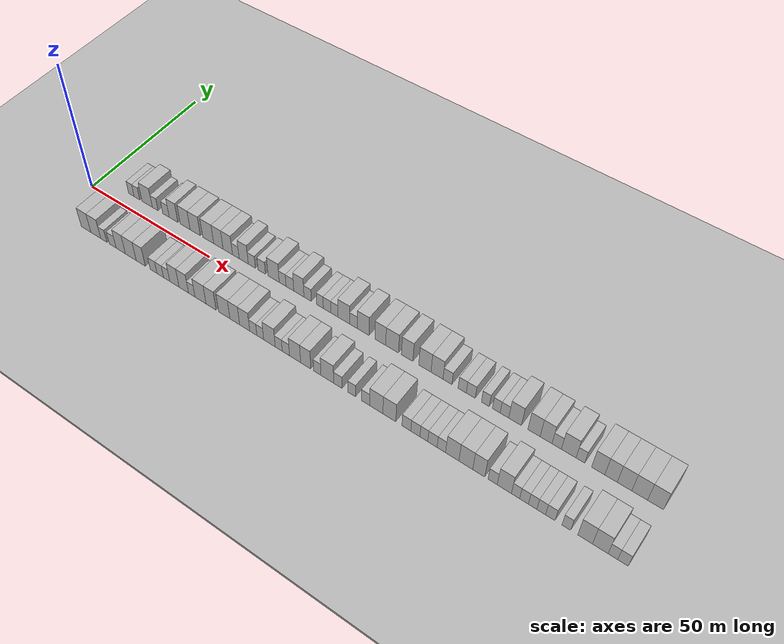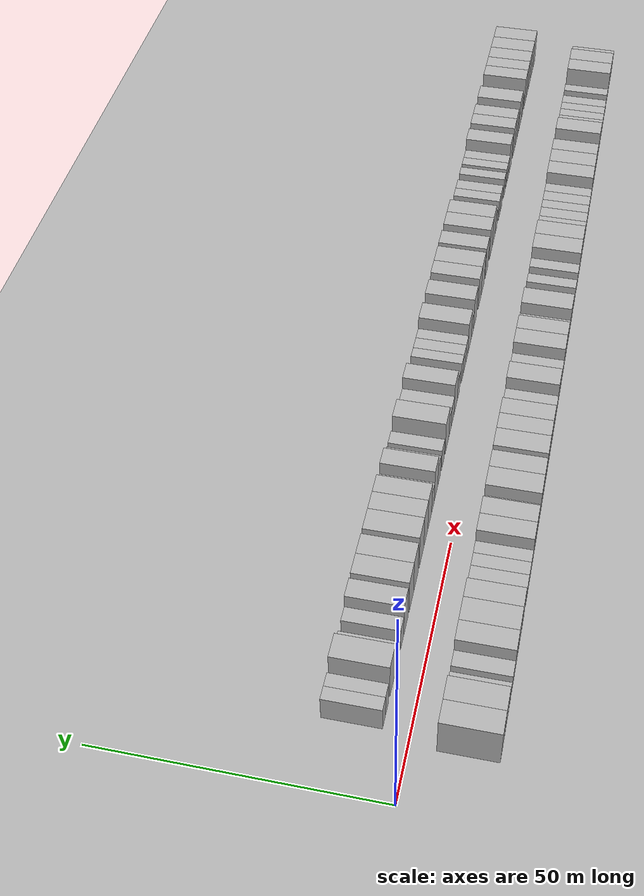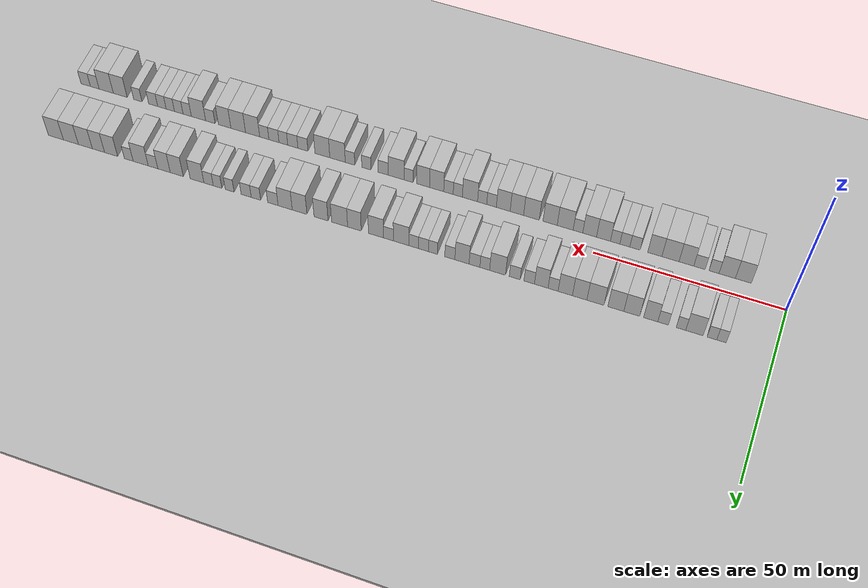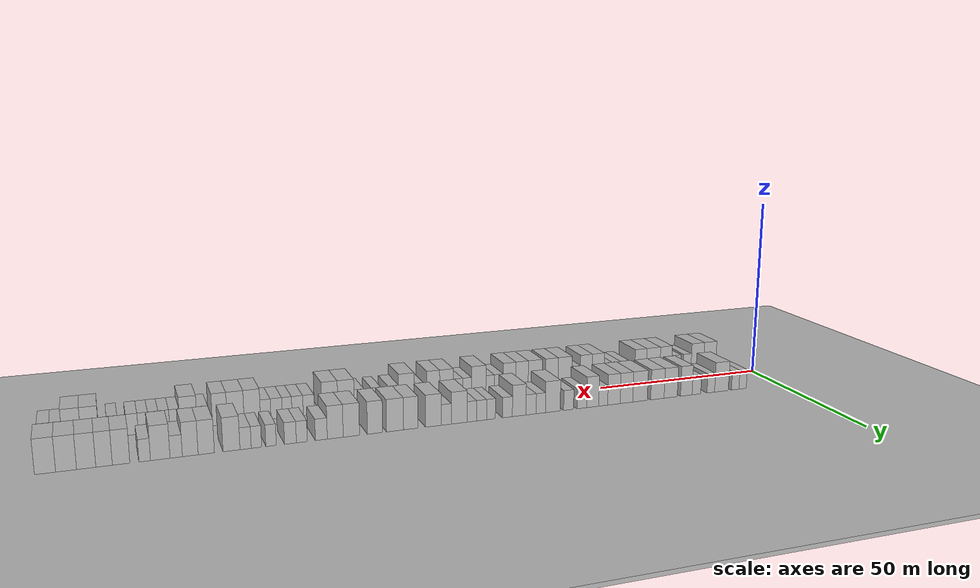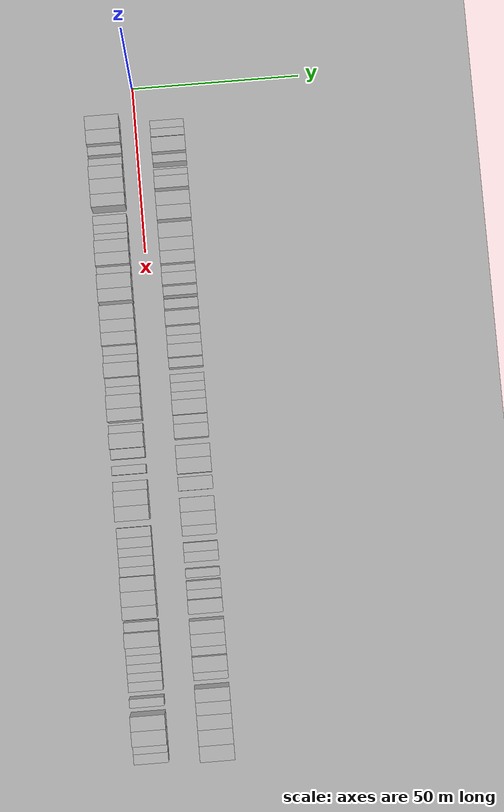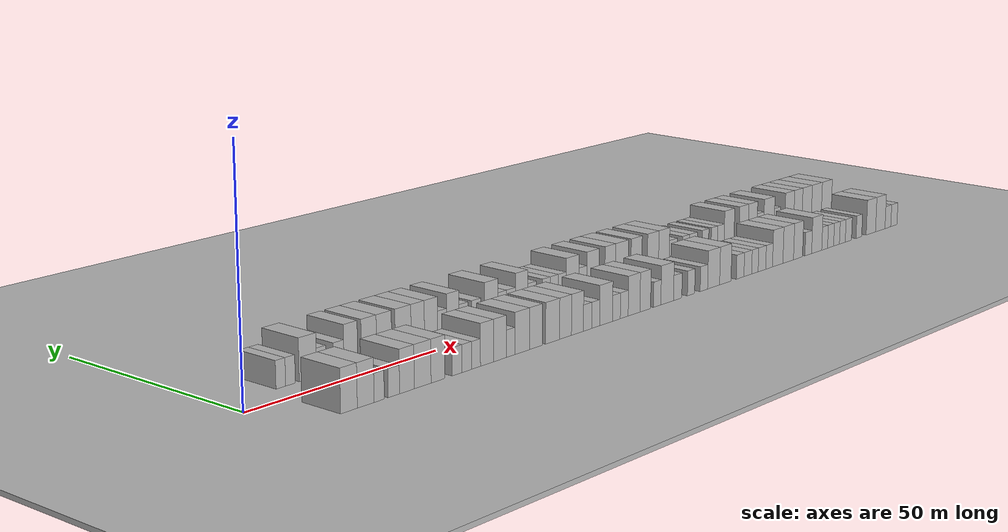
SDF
<?xml version="1.0" encoding="utf-8"?>

<sdf version="1.6">

   <world name="default">

      <gui fullscreen="0">

         <camera name="user_camera">

            <pose>-15 0 4.57585 0 0 0</pose>

            <view_controller>orbit</view_controller>

         </camera>

      </gui>

      <scene>

         <sky>

           <clouds>

             <speed>12</speed>

           </clouds>

         </sky>

         <ambient>0.4 0.4 0.4 1</ambient>

         <background>0.7 0.7 0.7 1</background>

         <shadows>1</shadows>

      </scene>

      <gravity>0 0 -9.8066</gravity>

      <magnetic_field>6e-06 2.3e-05 -4.2e-05</magnetic_field>

      <physics default="0" name="default_physics" type="ode">

         <ode>

            <solver>

               <type>quick</type>

               <iters>10</iters>

               <sor>1.0</sor>

               <use_dynamic_moi_rescaling>0</use_dynamic_moi_rescaling>

            </solver>

            <constraints>

               <cfm>0</cfm>

               <erp>0.2</erp>

               <contact_max_correcting_vel>100</contact_max_correcting_vel>

               <contact_surface_layer>0.001</contact_surface_layer>

            </constraints>

         </ode>

         <max_step_size>0.004</max_step_size>

         <real_time_factor>1</real_time_factor>

         <real_time_update_rate>250</real_time_update_rate>

      </physics>

      <light name="sun" type="directional">

         <cast_shadows>1</cast_shadows>

         <pose>0 0 10 0 0 0</pose>

         <diffuse>0.8 0.8 0.8 1</diffuse>

         <specular>0.2 0.2 0.2 1</specular>

         <attenuation>

            <range>1000</range>

            <constant>0.9</constant>

            <linear>0.01</linear>

            <quadratic>0.001</quadratic>

         </attenuation>

         <direction>-0.5 0.1 -0.9</direction>

      </light>

      <include>

         <name>ground_plane_1</name>

         <uri>model://HANNAS_ground_plane</uri>

         <pose>0 0 0  0 0 0</pose>

      </include>

      <include>

         <name>ground_plane_2</name>

         <uri>model://HANNAS_ground_plane</uri>

         <pose>100 0 0  0 0 0</pose>

      </include>

      <model name="building_1">

         <static>1</static>

         <pose frame="">13.2009 9.5000 0 0.000000 0.000000 1.570796</pose>

         <link name="link">

            <pose frame="">0 0 3.00 0 0 0</pose>

            <collision name="collision">

               <geometry>

                  <box>

                     <size>10.0000 2.4018 6.0000</size>

                  </box>

               </geometry>

               <max_contacts>10</max_contacts>

               <surface>

                  <contact>

                     <ode/>

                  </contact>

                  <bounce/>

                  <friction>

                     <torsional>

                        <ode/>

                     </torsional>

                     <ode/>

                  </friction>

               </surface>

            </collision>

            <visual name="visual">

               <cast_shadows>0</cast_shadows>

               <geometry>

                  <box>

                     <size>10.0000 2.4018 6.0000</size>

                  </box>

               </geometry>

               <material>

                  <script>

                     <uri>model://HANNAS_wall/materials/scripts</uri>

                     <uri>model://HANNAS_wall/materials/textures</uri>

                     <name>vrc/HANNAS_wall</name>

                  </script>

               </material>

            </visual>

            <self_collide>0</self_collide>

            <enable_wind>0</enable_wind>

            <kinematic>0</kinematic>

         </link>

      </model>

      <model name="building_2">

         <static>1</static>

         <pose frame="">15.6214 9.5000 0 0.000000 0.000000 1.570796</pose>

         <link name="link">

            <pose frame="">0 0 3.00 0 0 0</pose>

            <collision name="collision">

               <geometry>

                  <box>

                     <size>10.0000 2.4392 6.0000</size>

                  </box>

               </geometry>

               <max_contacts>10</max_contacts>

               <surface>

                  <contact>

                     <ode/>

                  </contact>

                  <bounce/>

                  <friction>

                     <torsional>

                        <ode/>

                     </torsional>

                     <ode/>

                  </friction>

               </surface>

            </collision>

            <visual name="visual">

               <cast_shadows>0</cast_shadows>

               <geometry>

                  <box>

                     <size>10.0000 2.4392 6.0000</size>

                  </box>

               </geometry>

               <material>

                  <script>

                     <uri>model://HANNAS_wall/materials/scripts</uri>

                     <uri>model://HANNAS_wall/materials/textures</uri>

                     <name>vrc/HANNAS_wall</name>

                  </script>

               </material>

            </visual>

            <self_collide>0</self_collide>

            <enable_wind>0</enable_wind>

            <kinematic>0</kinematic>

         </link>

      </model>

      <model name="building_3">

         <static>1</static>

         <pose frame="">20.0575 9.5000 0 0.000000 0.000000 1.570796</pose>

         <link name="link">

            <pose frame="">0 0 4.50 0 0 0</pose>

            <collision name="collision">

               <geometry>

                  <box>

                     <size>10.0000 4.4329 9.0000</size>

                  </box>

               </geometry>

               <max_contacts>10</max_contacts>

               <surface>

                  <contact>

                     <ode/>

                  </contact>

                  <bounce/>

                  <friction>

                     <torsional>

                        <ode/>

                     </torsional>

                     <ode/>

                  </friction>

               </surface>

            </collision>

            <visual name="visual">

               <cast_shadows>0</cast_shadows>

               <geometry>

                  <box>

                     <size>10.0000 4.4329 9.0000</size>

                  </box>

               </geometry>

               <material>

                  <script>

                     <uri>model://HANNAS_wall/materials/scripts</uri>

                     <uri>model://HANNAS_wall/materials/textures</uri>

                     <name>vrc/HANNAS_wall</name>

                  </script>

               </material>

            </visual>

            <self_collide>0</self_collide>

            <enable_wind>0</enable_wind>

            <kinematic>0</kinematic>

         </link>

      </model>

      <model name="building_4">

         <static>1</static>

         <pose frame="">23.4861 9.5000 0 0.000000 0.000000 1.570796</pose>

         <link name="link">

            <pose frame="">0 0 3.00 0 0 0</pose>

            <collision name="collision">

               <geometry>

                  <box>

                     <size>10.0000 2.4244 6.0000</size>

                  </box>

               </geometry>

               <max_contacts>10</max_contacts>

               <surface>

                  <contact>

                     <ode/>

                  </contact>

                  <bounce/>

                  <friction>

                     <torsional>

                        <ode/>

                     </torsional>

                     <ode/>

                  </friction>

               </surface>

            </collision>

            <visual name="visual">

               <cast_shadows>0</cast_shadows>

               <geometry>

                  <box>

                     <size>10.0000 2.4244 6.0000</size>

                  </box>

               </geometry>

               <material>

                  <script>

                     <uri>model://HANNAS_wall/materials/scripts</uri>

                     <uri>model://HANNAS_wall/materials/textures</uri>

                     <name>vrc/HANNAS_wall</name>

                  </script>

               </material>

            </visual>

            <self_collide>0</self_collide>

            <enable_wind>0</enable_wind>

            <kinematic>0</kinematic>

         </link>

      </model>

      <model name="building_5">

         <static>1</static>

         <pose frame="">28.0650 9.5000 0 0.000000 0.000000 1.570796</pose>

         <link name="link">

            <pose frame="">0 0 3.00 0 0 0</pose>

            <collision name="collision">

               <geometry>

                  <box>

                     <size>10.0000 2.7334 6.0000</size>

                  </box>

               </geometry>

               <max_contacts>10</max_contacts>

               <surface>

                  <contact>

                     <ode/>

                  </contact>

                  <bounce/>

                  <friction>

                     <torsional>

                        <ode/>

                     </torsional>

                     <ode/>

                  </friction>

               </surface>

            </collision>

            <visual name="visual">

               <cast_shadows>0</cast_shadows>

               <geometry>

                  <box>

                     <size>10.0000 2.7334 6.0000</size>

                  </box>

               </geometry>

               <material>

                  <script>

                     <uri>model://HANNAS_wall/materials/scripts</uri>

                     <uri>model://HANNAS_wall/materials/textures</uri>

                     <name>vrc/HANNAS_wall</name>

                  </script>

               </material>

            </visual>

            <self_collide>0</self_collide>

            <enable_wind>0</enable_wind>

            <kinematic>0</kinematic>

         </link>

      </model>

      <model name="building_6">

         <static>1</static>

         <pose frame="">31.2534 9.5000 0 0.000000 0.000000 1.570796</pose>

         <link name="link">

            <pose frame="">0 0 4.50 0 0 0</pose>

            <collision name="collision">

               <geometry>

                  <box>

                     <size>10.0000 3.6433 9.0000</size>

                  </box>

               </geometry>

               <max_contacts>10</max_contacts>

               <surface>

                  <contact>

                     <ode/>

                  </contact>

                  <bounce/>

                  <friction>

                     <torsional>

                        <ode/>

                     </torsional>

                     <ode/>

                  </friction>

               </surface>

            </collision>

            <visual name="visual">

               <cast_shadows>0</cast_shadows>

               <geometry>

                  <box>

                     <size>10.0000 3.6433 9.0000</size>

                  </box>

               </geometry>

               <material>

                  <script>

                     <uri>model://HANNAS_wall/materials/scripts</uri>

                     <uri>model://HANNAS_wall/materials/textures</uri>

                     <name>vrc/HANNAS_wall</name>

                  </script>

               </material>

            </visual>

            <self_collide>0</self_collide>

            <enable_wind>0</enable_wind>

            <kinematic>0</kinematic>

         </link>

      </model>

      <model name="building_7">

         <static>1</static>

         <pose frame="">36.1332 9.5000 0 0.000000 0.000000 1.570796</pose>

         <link name="link">

            <pose frame="">0 0 4.50 0 0 0</pose>

            <collision name="collision">

               <geometry>

                  <box>

                     <size>10.0000 4.1164 9.0000</size>

                  </box>

               </geometry>

               <max_contacts>10</max_contacts>

               <surface>

                  <contact>

                     <ode/>

                  </contact>

                  <bounce/>

                  <friction>

                     <torsional>

                        <ode/>

                     </torsional>

                     <ode/>

                  </friction>

               </surface>

            </collision>

            <visual name="visual">

               <cast_shadows>0</cast_shadows>

               <geometry>

                  <box>

                     <size>10.0000 4.1164 9.0000</size>

                  </box>

               </geometry>

               <material>

                  <script>

                     <uri>model://HANNAS_wall/materials/scripts</uri>

                     <uri>model://HANNAS_wall/materials/textures</uri>

                     <name>vrc/HANNAS_wall</name>

                  </script>

               </material>

            </visual>

            <self_collide>0</self_collide>

            <enable_wind>0</enable_wind>

            <kinematic>0</kinematic>

         </link>

      </model>

      <model name="building_8">

         <static>1</static>

         <pose frame="">40.2678 9.5000 0 0.000000 0.000000 1.570796</pose>

         <link name="link">

            <pose frame="">0 0 4.50 0 0 0</pose>

            <collision name="collision">

               <geometry>

                  <box>

                     <size>10.0000 4.1528 9.0000</size>

                  </box>

               </geometry>

               <max_contacts>10</max_contacts>

               <surface>

                  <contact>

                     <ode/>

                  </contact>

                  <bounce/>

                  <friction>

                     <torsional>

                        <ode/>

                     </torsional>

                     <ode/>

                  </friction>

               </surface>

            </collision>

            <visual name="visual">

               <cast_shadows>0</cast_shadows>

               <geometry>

                  <box>

                     <size>10.0000 4.1528 9.0000</size>

                  </box>

               </geometry>

               <material>

                  <script>

                     <uri>model://HANNAS_wall/materials/scripts</uri>

                     <uri>model://HANNAS_wall/materials/textures</uri>

                     <name>vrc/HANNAS_wall</name>

                  </script>

               </material>

            </visual>

            <self_collide>0</self_collide>

            <enable_wind>0</enable_wind>

            <kinematic>0</kinematic>

         </link>

      </model>

      <model name="building_9">

         <static>1</static>

         <pose frame="">45.5697 9.5000 0 0.000000 0.000000 1.570796</pose>

         <link name="link">

            <pose frame="">0 0 4.50 0 0 0</pose>

            <collision name="collision">

               <geometry>

                  <box>

                     <size>10.0000 4.4511 9.0000</size>

                  </box>

               </geometry>

               <max_contacts>10</max_contacts>

               <surface>

                  <contact>

                     <ode/>

                  </contact>

                  <bounce/>

                  <friction>

                     <torsional>

                        <ode/>

                     </torsional>

                     <ode/>

                  </friction>

               </surface>

            </collision>

            <visual name="visual">

               <cast_shadows>0</cast_shadows>

               <geometry>

                  <box>

                     <size>10.0000 4.4511 9.0000</size>

                  </box>

               </geometry>

               <material>

                  <script>

                     <uri>model://HANNAS_wall/materials/scripts</uri>

                     <uri>model://HANNAS_wall/materials/textures</uri>

                     <name>vrc/HANNAS_wall</name>

                  </script>

               </material>

            </visual>

            <self_collide>0</self_collide>

            <enable_wind>0</enable_wind>

            <kinematic>0</kinematic>

         </link>

      </model>

      <model name="building_10">

         <static>1</static>

         <pose frame="">49.6884 9.5000 0 0.000000 0.000000 1.570796</pose>

         <link name="link">

            <pose frame="">0 0 4.50 0 0 0</pose>

            <collision name="collision">

               <geometry>

                  <box>

                     <size>10.0000 3.7864 9.0000</size>

                  </box>

               </geometry>

               <max_contacts>10</max_contacts>

               <surface>

                  <contact>

                     <ode/>

                  </contact>

                  <bounce/>

                  <friction>

                     <torsional>

                        <ode/>

                     </torsional>

                     <ode/>

                  </friction>

               </surface>

            </collision>

            <visual name="visual">

               <cast_shadows>0</cast_shadows>

               <geometry>

                  <box>

                     <size>10.0000 3.7864 9.0000</size>

                  </box>

               </geometry>

               <material>

                  <script>

                     <uri>model://HANNAS_wall/materials/scripts</uri>

                     <uri>model://HANNAS_wall/materials/textures</uri>

                     <name>vrc/HANNAS_wall</name>

                  </script>

               </material>

            </visual>

            <self_collide>0</self_collide>

            <enable_wind>0</enable_wind>

            <kinematic>0</kinematic>

         </link>

      </model>

      <model name="building_11">

         <static>1</static>

         <pose frame="">53.4665 9.5000 0 0.000000 0.000000 1.570796</pose>

         <link name="link">

            <pose frame="">0 0 4.50 0 0 0</pose>

            <collision name="collision">

               <geometry>

                  <box>

                     <size>10.0000 3.7699 9.0000</size>

                  </box>

               </geometry>

               <max_contacts>10</max_contacts>

               <surface>

                  <contact>

                     <ode/>

                  </contact>

                  <bounce/>

                  <friction>

                     <torsional>

                        <ode/>

                     </torsional>

                     <ode/>

                  </friction>

               </surface>

            </collision>

            <visual name="visual">

               <cast_shadows>0</cast_shadows>

               <geometry>

                  <box>

                     <size>10.0000 3.7699 9.0000</size>

                  </box>

               </geometry>

               <material>

                  <script>

                     <uri>model://HANNAS_wall/materials/scripts</uri>

                     <uri>model://HANNAS_wall/materials/textures</uri>

                     <name>vrc/HANNAS_wall</name>

                  </script>

               </material>

            </visual>

            <self_collide>0</self_collide>

            <enable_wind>0</enable_wind>

            <kinematic>0</kinematic>

         </link>

      </model>

      <model name="building_12">

         <static>1</static>

         <pose frame="">56.6749 9.5000 0 0.000000 0.000000 1.570796</pose>

         <link name="link">

            <pose frame="">0 0 3.00 0 0 0</pose>

            <collision name="collision">

               <geometry>

                  <box>

                     <size>10.0000 2.6469 6.0000</size>

                  </box>

               </geometry>

               <max_contacts>10</max_contacts>

               <surface>

                  <contact>

                     <ode/>

                  </contact>

                  <bounce/>

                  <friction>

                     <torsional>

                        <ode/>

                     </torsional>

                     <ode/>

                  </friction>

               </surface>

            </collision>

            <visual name="visual">

               <cast_shadows>0</cast_shadows>

               <geometry>

                  <box>

                     <size>10.0000 2.6469 6.0000</size>

                  </box>

               </geometry>

               <material>

                  <script>

                     <uri>model://HANNAS_wall/materials/scripts</uri>

                     <uri>model://HANNAS_wall/materials/textures</uri>

                     <name>vrc/HANNAS_wall</name>

                  </script>

               </material>

            </visual>

            <self_collide>0</self_collide>

            <enable_wind>0</enable_wind>

            <kinematic>0</kinematic>

         </link>

      </model>

      <model name="building_13">

         <static>1</static>

         <pose frame="">59.8021 9.5000 0 0.000000 0.000000 1.570796</pose>

         <link name="link">

            <pose frame="">0 0 4.50 0 0 0</pose>

            <collision name="collision">

               <geometry>

                  <box>

                     <size>10.0000 3.6074 9.0000</size>

                  </box>

               </geometry>

               <max_contacts>10</max_contacts>

               <surface>

                  <contact>

                     <ode/>

                  </contact>

                  <bounce/>

                  <friction>

                     <torsional>

                        <ode/>

                     </torsional>

                     <ode/>

                  </friction>

               </surface>

            </collision>

            <visual name="visual">

               <cast_shadows>0</cast_shadows>

               <geometry>

                  <box>

                     <size>10.0000 3.6074 9.0000</size>

                  </box>

               </geometry>

               <material>

                  <script>

                     <uri>model://HANNAS_wall/materials/scripts</uri>

                     <uri>model://HANNAS_wall/materials/textures</uri>

                     <name>vrc/HANNAS_wall</name>

                  </script>

               </material>

            </visual>

            <self_collide>0</self_collide>

            <enable_wind>0</enable_wind>

            <kinematic>0</kinematic>

         </link>

      </model>

      <model name="building_14">

         <static>1</static>

         <pose frame="">62.9990 9.5000 0 0.000000 0.000000 1.570796</pose>

         <link name="link">

            <pose frame="">0 0 3.00 0 0 0</pose>

            <collision name="collision">

               <geometry>

                  <box>

                     <size>10.0000 2.7863 6.0000</size>

                  </box>

               </geometry>

               <max_contacts>10</max_contacts>

               <surface>

                  <contact>

                     <ode/>

                  </contact>

                  <bounce/>

                  <friction>

                     <torsional>

                        <ode/>

                     </torsional>

                     <ode/>

                  </friction>

               </surface>

            </collision>

            <visual name="visual">

               <cast_shadows>0</cast_shadows>

               <geometry>

                  <box>

                     <size>10.0000 2.7863 6.0000</size>

                  </box>

               </geometry>

               <material>

                  <script>

                     <uri>model://HANNAS_wall/materials/scripts</uri>

                     <uri>model://HANNAS_wall/materials/textures</uri>

                     <name>vrc/HANNAS_wall</name>

                  </script>

               </material>

            </visual>

            <self_collide>0</self_collide>

            <enable_wind>0</enable_wind>

            <kinematic>0</kinematic>

         </link>

      </model>

      <model name="building_15">

         <static>1</static>

         <pose frame="">66.8401 9.5000 0 0.000000 0.000000 1.570796</pose>

         <link name="link">

            <pose frame="">0 0 3.00 0 0 0</pose>

            <collision name="collision">

               <geometry>

                  <box>

                     <size>10.0000 2.8960 6.0000</size>

                  </box>

               </geometry>

               <max_contacts>10</max_contacts>

               <surface>

                  <contact>

                     <ode/>

                  </contact>

                  <bounce/>

                  <friction>

                     <torsional>

                        <ode/>

                     </torsional>

                     <ode/>

                  </friction>

               </surface>

            </collision>

            <visual name="visual">

               <cast_shadows>0</cast_shadows>

               <geometry>

                  <box>

                     <size>10.0000 2.8960 6.0000</size>

                  </box>

               </geometry>

               <material>

                  <script>

                     <uri>model://HANNAS_wall/materials/scripts</uri>

                     <uri>model://HANNAS_wall/materials/textures</uri>

                     <name>vrc/HANNAS_wall</name>

                  </script>

               </material>

            </visual>

            <self_collide>0</self_collide>

            <enable_wind>0</enable_wind>

            <kinematic>0</kinematic>

         </link>

      </model>

      <model name="building_16">

         <static>1</static>

         <pose frame="">71.4126 9.5000 0 0.000000 0.000000 1.570796</pose>

         <link name="link">

            <pose frame="">0 0 4.50 0 0 0</pose>

            <collision name="collision">

               <geometry>

                  <box>

                     <size>10.0000 4.2489 9.0000</size>

                  </box>

               </geometry>

               <max_contacts>10</max_contacts>

               <surface>

                  <contact>

                     <ode/>

                  </contact>

                  <bounce/>

                  <friction>

                     <torsional>

                        <ode/>

                     </torsional>

                     <ode/>

                  </friction>

               </surface>

            </collision>

            <visual name="visual">

               <cast_shadows>0</cast_shadows>

               <geometry>

                  <box>

                     <size>10.0000 4.2489 9.0000</size>

                  </box>

               </geometry>

               <material>

                  <script>

                     <uri>model://HANNAS_wall/materials/scripts</uri>

                     <uri>model://HANNAS_wall/materials/textures</uri>

                     <name>vrc/HANNAS_wall</name>

                  </script>

               </material>

            </visual>

            <self_collide>0</self_collide>

            <enable_wind>0</enable_wind>

            <kinematic>0</kinematic>

         </link>

      </model>

      <model name="building_17">

         <static>1</static>

         <pose frame="">74.8411 9.5000 0 0.000000 0.000000 1.570796</pose>

         <link name="link">

            <pose frame="">0 0 3.00 0 0 0</pose>

            <collision name="collision">

               <geometry>

                  <box>

                     <size>10.0000 2.6082 6.0000</size>

                  </box>

               </geometry>

               <max_contacts>10</max_contacts>

               <surface>

                  <contact>

                     <ode/>

                  </contact>

                  <bounce/>

                  <friction>

                     <torsional>

                        <ode/>

                     </torsional>

                     <ode/>

                  </friction>

               </surface>

            </collision>

            <visual name="visual">

               <cast_shadows>0</cast_shadows>

               <geometry>

                  <box>

                     <size>10.0000 2.6082 6.0000</size>

                  </box>

               </geometry>

               <material>

                  <script>

                     <uri>model://HANNAS_wall/materials/scripts</uri>

                     <uri>model://HANNAS_wall/materials/textures</uri>

                     <name>vrc/HANNAS_wall</name>

                  </script>

               </material>

            </visual>

            <self_collide>0</self_collide>

            <enable_wind>0</enable_wind>

            <kinematic>0</kinematic>

         </link>

      </model>

      <model name="building_18">

         <static>1</static>

         <pose frame="">77.6003 9.5000 0 0.000000 0.000000 1.570796</pose>

         <link name="link">

            <pose frame="">0 0 3.00 0 0 0</pose>

            <collision name="collision">

               <geometry>

                  <box>

                     <size>10.0000 2.9102 6.0000</size>

                  </box>

               </geometry>

               <max_contacts>10</max_contacts>

               <surface>

                  <contact>

                     <ode/>

                  </contact>

                  <bounce/>

                  <friction>

                     <torsional>

                        <ode/>

                     </torsional>

                     <ode/>

                  </friction>

               </surface>

            </collision>

            <visual name="visual">

               <cast_shadows>0</cast_shadows>

               <geometry>

                  <box>

                     <size>10.0000 2.9102 6.0000</size>

                  </box>

               </geometry>

               <material>

                  <script>

                     <uri>model://HANNAS_wall/materials/scripts</uri>

                     <uri>model://HANNAS_wall/materials/textures</uri>

                     <name>vrc/HANNAS_wall</name>

                  </script>

               </material>

            </visual>

            <self_collide>0</self_collide>

            <enable_wind>0</enable_wind>

            <kinematic>0</kinematic>

         </link>

      </model>

      <model name="building_19">

         <static>1</static>

         <pose frame="">80.9687 9.5000 0 0.000000 0.000000 1.570796</pose>

         <link name="link">

            <pose frame="">0 0 4.50 0 0 0</pose>

            <collision name="collision">

               <geometry>

                  <box>

                     <size>10.0000 3.8265 9.0000</size>

                  </box>

               </geometry>

               <max_contacts>10</max_contacts>

               <surface>

                  <contact>

                     <ode/>

                  </contact>

                  <bounce/>

                  <friction>

                     <torsional>

                        <ode/>

                     </torsional>

                     <ode/>

                  </friction>

               </surface>

            </collision>

            <visual name="visual">

               <cast_shadows>0</cast_shadows>

               <geometry>

                  <box>

                     <size>10.0000 3.8265 9.0000</size>

                  </box>

               </geometry>

               <material>

                  <script>

                     <uri>model://HANNAS_wall/materials/scripts</uri>

                     <uri>model://HANNAS_wall/materials/textures</uri>

                     <name>vrc/HANNAS_wall</name>

                  </script>

               </material>

            </visual>

            <self_collide>0</self_collide>

            <enable_wind>0</enable_wind>

            <kinematic>0</kinematic>

         </link>

      </model>

      <model name="building_20">

         <static>1</static>

         <pose frame="">84.2531 9.5000 0 0.000000 0.000000 1.570796</pose>

         <link name="link">

            <pose frame="">0 0 3.00 0 0 0</pose>

            <collision name="collision">

               <geometry>

                  <box>

                     <size>10.0000 2.7424 6.0000</size>

                  </box>

               </geometry>

               <max_contacts>10</max_contacts>

               <surface>

                  <contact>

                     <ode/>

                  </contact>

                  <bounce/>

                  <friction>

                     <torsional>

                        <ode/>

                     </torsional>

                     <ode/>

                  </friction>

               </surface>

            </collision>

            <visual name="visual">

               <cast_shadows>0</cast_shadows>

               <geometry>

                  <box>

                     <size>10.0000 2.7424 6.0000</size>

                  </box>

               </geometry>

               <material>

                  <script>

                     <uri>model://HANNAS_wall/materials/scripts</uri>

                     <uri>model://HANNAS_wall/materials/textures</uri>

                     <name>vrc/HANNAS_wall</name>

                  </script>

               </material>

            </visual>

            <self_collide>0</self_collide>

            <enable_wind>0</enable_wind>

            <kinematic>0</kinematic>

         </link>

      </model>

      <model name="building_21">

         <static>1</static>

         <pose frame="">88.8378 9.5000 0 0.000000 0.000000 1.570796</pose>

         <link name="link">

            <pose frame="">0 0 3.00 0 0 0</pose>

            <collision name="collision">

               <geometry>

                  <box>

                     <size>10.0000 2.4270 6.0000</size>

                  </box>

               </geometry>

               <max_contacts>10</max_contacts>

               <surface>

                  <contact>

                     <ode/>

                  </contact>

                  <bounce/>

                  <friction>

                     <torsional>

                        <ode/>

                     </torsional>

                     <ode/>

                  </friction>

               </surface>

            </collision>

            <visual name="visual">

               <cast_shadows>0</cast_shadows>

               <geometry>

                  <box>

                     <size>10.0000 2.4270 6.0000</size>

                  </box>

               </geometry>

               <material>

                  <script>

                     <uri>model://HANNAS_wall/materials/scripts</uri>

                     <uri>model://HANNAS_wall/materials/textures</uri>

                     <name>vrc/HANNAS_wall</name>

                  </script>

               </material>

            </visual>

            <self_collide>0</self_collide>

            <enable_wind>0</enable_wind>

            <kinematic>0</kinematic>

         </link>

      </model>

      <model name="building_22">

         <static>1</static>

         <pose frame="">91.4158 9.5000 0 0.000000 0.000000 1.570796</pose>

         <link name="link">

            <pose frame="">0 0 3.00 0 0 0</pose>

            <collision name="collision">

               <geometry>

                  <box>

                     <size>10.0000 2.7290 6.0000</size>

                  </box>

               </geometry>

               <max_contacts>10</max_contacts>

               <surface>

                  <contact>

                     <ode/>

                  </contact>

                  <bounce/>

                  <friction>

                     <torsional>

                        <ode/>

                     </torsional>

                     <ode/>

                  </friction>

               </surface>

            </collision>

            <visual name="visual">

               <cast_shadows>0</cast_shadows>

               <geometry>

                  <box>

                     <size>10.0000 2.7290 6.0000</size>

                  </box>

               </geometry>

               <material>

                  <script>

                     <uri>model://HANNAS_wall/materials/scripts</uri>

                     <uri>model://HANNAS_wall/materials/textures</uri>

                     <name>vrc/HANNAS_wall</name>

                  </script>

               </material>

            </visual>

            <self_collide>0</self_collide>

            <enable_wind>0</enable_wind>

            <kinematic>0</kinematic>

         </link>

      </model>

      <model name="building_23">

         <static>1</static>

         <pose frame="">94.0646 9.5000 0 0.000000 0.000000 1.570796</pose>

         <link name="link">

            <pose frame="">0 0 3.00 0 0 0</pose>

            <collision name="collision">

               <geometry>

                  <box>

                     <size>10.0000 2.5685 6.0000</size>

                  </box>

               </geometry>

               <max_contacts>10</max_contacts>

               <surface>

                  <contact>

                     <ode/>

                  </contact>

                  <bounce/>

                  <friction>

                     <torsional>

                        <ode/>

                     </torsional>

                     <ode/>

                  </friction>

               </surface>

            </collision>

            <visual name="visual">

               <cast_shadows>0</cast_shadows>

               <geometry>

                  <box>

                     <size>10.0000 2.5685 6.0000</size>

                  </box>

               </geometry>

               <material>

                  <script>

                     <uri>model://HANNAS_wall/materials/scripts</uri>

                     <uri>model://HANNAS_wall/materials/textures</uri>

                     <name>vrc/HANNAS_wall</name>

                  </script>

               </material>

            </visual>

            <self_collide>0</self_collide>

            <enable_wind>0</enable_wind>

            <kinematic>0</kinematic>

         </link>

      </model>

      <model name="building_24">

         <static>1</static>

         <pose frame="">97.5057 9.5000 0 0.000000 0.000000 1.570796</pose>

         <link name="link">

            <pose frame="">0 0 4.50 0 0 0</pose>

            <collision name="collision">

               <geometry>

                  <box>

                     <size>10.0000 4.3137 9.0000</size>

                  </box>

               </geometry>

               <max_contacts>10</max_contacts>

               <surface>

                  <contact>

                     <ode/>

                  </contact>

                  <bounce/>

                  <friction>

                     <torsional>

                        <ode/>

                     </torsional>

                     <ode/>

                  </friction>

               </surface>

            </collision>

            <visual name="visual">

               <cast_shadows>0</cast_shadows>

               <geometry>

                  <box>

                     <size>10.0000 4.3137 9.0000</size>

                  </box>

               </geometry>

               <material>

                  <script>

                     <uri>model://HANNAS_wall/materials/scripts</uri>

                     <uri>model://HANNAS_wall/materials/textures</uri>

                     <name>vrc/HANNAS_wall</name>

                  </script>

               </material>

            </visual>

            <self_collide>0</self_collide>

            <enable_wind>0</enable_wind>

            <kinematic>0</kinematic>

         </link>

      </model>

      <model name="building_25">

         <static>1</static>

         <pose frame="">101.0171 9.5000 0 0.000000 0.000000 1.570796</pose>

         <link name="link">

            <pose frame="">0 0 3.00 0 0 0</pose>

            <collision name="collision">

               <geometry>

                  <box>

                     <size>10.0000 2.7090 6.0000</size>

                  </box>

               </geometry>

               <max_contacts>10</max_contacts>

               <surface>

                  <contact>

                     <ode/>

                  </contact>

                  <bounce/>

                  <friction>

                     <torsional>

                        <ode/>

                     </torsional>

                     <ode/>

                  </friction>

               </surface>

            </collision>

            <visual name="visual">

               <cast_shadows>0</cast_shadows>

               <geometry>

                  <box>

                     <size>10.0000 2.7090 6.0000</size>

                  </box>

               </geometry>

               <material>

                  <script>

                     <uri>model://HANNAS_wall/materials/scripts</uri>

                     <uri>model://HANNAS_wall/materials/textures</uri>

                     <name>vrc/HANNAS_wall</name>

                  </script>

               </material>

            </visual>

            <self_collide>0</self_collide>

            <enable_wind>0</enable_wind>

            <kinematic>0</kinematic>

         </link>

      </model>

      <model name="building_26">

         <static>1</static>

         <pose frame="">104.4458 9.5000 0 0.000000 0.000000 1.570796</pose>

         <link name="link">

            <pose frame="">0 0 4.50 0 0 0</pose>

            <collision name="collision">

               <geometry>

                  <box>

                     <size>10.0000 4.1483 9.0000</size>

                  </box>

               </geometry>

               <max_contacts>10</max_contacts>

               <surface>

                  <contact>

                     <ode/>

                  </contact>

                  <bounce/>

                  <friction>

                     <torsional>

                        <ode/>

                     </torsional>

                     <ode/>

                  </friction>

               </surface>

            </collision>

            <visual name="visual">

               <cast_shadows>0</cast_shadows>

               <geometry>

                  <box>

                     <size>10.0000 4.1483 9.0000</size>

                  </box>

               </geometry>

               <material>

                  <script>

                     <uri>model://HANNAS_wall/materials/scripts</uri>

                     <uri>model://HANNAS_wall/materials/textures</uri>

                     <name>vrc/HANNAS_wall</name>

                  </script>

               </material>

            </visual>

            <self_collide>0</self_collide>

            <enable_wind>0</enable_wind>

            <kinematic>0</kinematic>

         </link>

      </model>

      <model name="building_27">

         <static>1</static>

         <pose frame="">110.4118 9.5000 0 0.000000 0.000000 1.570796</pose>

         <link name="link">

            <pose frame="">0 0 4.50 0 0 0</pose>

            <collision name="collision">

               <geometry>

                  <box>

                     <size>10.0000 3.7836 9.0000</size>

                  </box>

               </geometry>

               <max_contacts>10</max_contacts>

               <surface>

                  <contact>

                     <ode/>

                  </contact>

                  <bounce/>

                  <friction>

                     <torsional>

                        <ode/>

                     </torsional>

                     <ode/>

                  </friction>

               </surface>

            </collision>

            <visual name="visual">

               <cast_shadows>0</cast_shadows>

               <geometry>

                  <box>

                     <size>10.0000 3.7836 9.0000</size>

                  </box>

               </geometry>

               <material>

                  <script>

                     <uri>model://HANNAS_wall/materials/scripts</uri>

                     <uri>model://HANNAS_wall/materials/textures</uri>

                     <name>vrc/HANNAS_wall</name>

                  </script>

               </material>

            </visual>

            <self_collide>0</self_collide>

            <enable_wind>0</enable_wind>

            <kinematic>0</kinematic>

         </link>

      </model>

      <model name="building_28">

         <static>1</static>

         <pose frame="">114.5267 9.5000 0 0.000000 0.000000 1.570796</pose>

         <link name="link">

            <pose frame="">0 0 4.50 0 0 0</pose>

            <collision name="collision">

               <geometry>

                  <box>

                     <size>10.0000 4.4463 9.0000</size>

                  </box>

               </geometry>

               <max_contacts>10</max_contacts>

               <surface>

                  <contact>

                     <ode/>

                  </contact>

                  <bounce/>

                  <friction>

                     <torsional>

                        <ode/>

                     </torsional>

                     <ode/>

                  </friction>

               </surface>

            </collision>

            <visual name="visual">

               <cast_shadows>0</cast_shadows>

               <geometry>

                  <box>

                     <size>10.0000 4.4463 9.0000</size>

                  </box>

               </geometry>

               <material>

                  <script>

                     <uri>model://HANNAS_wall/materials/scripts</uri>

                     <uri>model://HANNAS_wall/materials/textures</uri>

                     <name>vrc/HANNAS_wall</name>

                  </script>

               </material>

            </visual>

            <self_collide>0</self_collide>

            <enable_wind>0</enable_wind>

            <kinematic>0</kinematic>

         </link>

      </model>

      <model name="building_29">

         <static>1</static>

         <pose frame="">119.7096 9.5000 0 0.000000 0.000000 1.570796</pose>

         <link name="link">

            <pose frame="">0 0 4.50 0 0 0</pose>

            <collision name="collision">

               <geometry>

                  <box>

                     <size>10.0000 3.9195 9.0000</size>

                  </box>

               </geometry>

               <max_contacts>10</max_contacts>

               <surface>

                  <contact>

                     <ode/>

                  </contact>

                  <bounce/>

                  <friction>

                     <torsional>

                        <ode/>

                     </torsional>

                     <ode/>

                  </friction>

               </surface>

            </collision>

            <visual name="visual">

               <cast_shadows>0</cast_shadows>

               <geometry>

                  <box>

                     <size>10.0000 3.9195 9.0000</size>

                  </box>

               </geometry>

               <material>

                  <script>

                     <uri>model://HANNAS_wall/materials/scripts</uri>

                     <uri>model://HANNAS_wall/materials/textures</uri>

                     <name>vrc/HANNAS_wall</name>

                  </script>

               </material>

            </visual>

            <self_collide>0</self_collide>

            <enable_wind>0</enable_wind>

            <kinematic>0</kinematic>

         </link>

      </model>

      <model name="building_30">

         <static>1</static>

         <pose frame="">125.7354 9.5000 0 0.000000 0.000000 1.570796</pose>

         <link name="link">

            <pose frame="">0 0 4.50 0 0 0</pose>

            <collision name="collision">

               <geometry>

                  <box>

                     <size>10.0000 4.1321 9.0000</size>

                  </box>

               </geometry>

               <max_contacts>10</max_contacts>

               <surface>

                  <contact>

                     <ode/>

                  </contact>

                  <bounce/>

                  <friction>

                     <torsional>

                        <ode/>

                     </torsional>

                     <ode/>

                  </friction>

               </surface>

            </collision>

            <visual name="visual">

               <cast_shadows>0</cast_shadows>

               <geometry>

                  <box>

                     <size>10.0000 4.1321 9.0000</size>

                  </box>

               </geometry>

               <material>

                  <script>

                     <uri>model://HANNAS_wall/materials/scripts</uri>

                     <uri>model://HANNAS_wall/materials/textures</uri>

                     <name>vrc/HANNAS_wall</name>

                  </script>

               </material>

            </visual>

            <self_collide>0</self_collide>

            <enable_wind>0</enable_wind>

            <kinematic>0</kinematic>

         </link>

      </model>

      <model name="building_31">

         <static>1</static>

         <pose frame="">129.7963 9.5000 0 0.000000 0.000000 1.570796</pose>

         <link name="link">

            <pose frame="">0 0 4.50 0 0 0</pose>

            <collision name="collision">

               <geometry>

                  <box>

                     <size>10.0000 3.9898 9.0000</size>

                  </box>

               </geometry>

               <max_contacts>10</max_contacts>

               <surface>

                  <contact>

                     <ode/>

                  </contact>

                  <bounce/>

                  <friction>

                     <torsional>

                        <ode/>

                     </torsional>

                     <ode/>

                  </friction>

               </surface>

            </collision>

            <visual name="visual">

               <cast_shadows>0</cast_shadows>

               <geometry>

                  <box>

                     <size>10.0000 3.9898 9.0000</size>

                  </box>

               </geometry>

               <material>

                  <script>

                     <uri>model://HANNAS_wall/materials/scripts</uri>

                     <uri>model://HANNAS_wall/materials/textures</uri>

                     <name>vrc/HANNAS_wall</name>

                  </script>

               </material>

            </visual>

            <self_collide>0</self_collide>

            <enable_wind>0</enable_wind>

            <kinematic>0</kinematic>

         </link>

      </model>

      <model name="building_32">

         <static>1</static>

         <pose frame="">133.2743 9.5000 0 0.000000 0.000000 1.570796</pose>

         <link name="link">

            <pose frame="">0 0 3.00 0 0 0</pose>

            <collision name="collision">

               <geometry>

                  <box>

                     <size>10.0000 2.9662 6.0000</size>

                  </box>

               </geometry>

               <max_contacts>10</max_contacts>

               <surface>

                  <contact>

                     <ode/>

                  </contact>

                  <bounce/>

                  <friction>

                     <torsional>

                        <ode/>

                     </torsional>

                     <ode/>

                  </friction>

               </surface>

            </collision>

            <visual name="visual">

               <cast_shadows>0</cast_shadows>

               <geometry>

                  <box>

                     <size>10.0000 2.9662 6.0000</size>

                  </box>

               </geometry>

               <material>

                  <script>

                     <uri>model://HANNAS_wall/materials/scripts</uri>

                     <uri>model://HANNAS_wall/materials/textures</uri>

                     <name>vrc/HANNAS_wall</name>

                  </script>

               </material>

            </visual>

            <self_collide>0</self_collide>

            <enable_wind>0</enable_wind>

            <kinematic>0</kinematic>

         </link>

      </model>

      <model name="building_33">

         <static>1</static>

         <pose frame="">138.0981 9.5000 0 0.000000 0.000000 1.570796</pose>

         <link name="link">

            <pose frame="">0 0 3.00 0 0 0</pose>

            <collision name="collision">

               <geometry>

                  <box>

                     <size>10.0000 2.6814 6.0000</size>

                  </box>

               </geometry>

               <max_contacts>10</max_contacts>

               <surface>

                  <contact>

                     <ode/>

                  </contact>

                  <bounce/>

                  <friction>

                     <torsional>

                        <ode/>

                     </torsional>

                     <ode/>

                  </friction>

               </surface>

            </collision>

            <visual name="visual">

               <cast_shadows>0</cast_shadows>

               <geometry>

                  <box>

                     <size>10.0000 2.6814 6.0000</size>

                  </box>

               </geometry>

               <material>

                  <script>

                     <uri>model://HANNAS_wall/materials/scripts</uri>

                     <uri>model://HANNAS_wall/materials/textures</uri>

                     <name>vrc/HANNAS_wall</name>

                  </script>

               </material>

            </visual>

            <self_collide>0</self_collide>

            <enable_wind>0</enable_wind>

            <kinematic>0</kinematic>

         </link>

      </model>

      <model name="building_34">

         <static>1</static>

         <pose frame="">140.8822 9.5000 0 0.000000 0.000000 1.570796</pose>

         <link name="link">

            <pose frame="">0 0 3.00 0 0 0</pose>

            <collision name="collision">

               <geometry>

                  <box>

                     <size>10.0000 2.8869 6.0000</size>

                  </box>

               </geometry>

               <max_contacts>10</max_contacts>

               <surface>

                  <contact>

                     <ode/>

                  </contact>

                  <bounce/>

                  <friction>

                     <torsional>

                        <ode/>

                     </torsional>

                     <ode/>

                  </friction>

               </surface>

            </collision>

            <visual name="visual">

               <cast_shadows>0</cast_shadows>

               <geometry>

                  <box>

                     <size>10.0000 2.8869 6.0000</size>

                  </box>

               </geometry>

               <material>

                  <script>

                     <uri>model://HANNAS_wall/materials/scripts</uri>

                     <uri>model://HANNAS_wall/materials/textures</uri>

                     <name>vrc/HANNAS_wall</name>

                  </script>

               </material>

            </visual>

            <self_collide>0</self_collide>

            <enable_wind>0</enable_wind>

            <kinematic>0</kinematic>

         </link>

      </model>

      <model name="building_35">

         <static>1</static>

         <pose frame="">145.5830 9.5000 0 0.000000 0.000000 1.570796</pose>

         <link name="link">

            <pose frame="">0 0 3.00 0 0 0</pose>

            <collision name="collision">

               <geometry>

                  <box>

                     <size>10.0000 2.5147 6.0000</size>

                  </box>

               </geometry>

               <max_contacts>10</max_contacts>

               <surface>

                  <contact>

                     <ode/>

                  </contact>

                  <bounce/>

                  <friction>

                     <torsional>

                        <ode/>

                     </torsional>

                     <ode/>

                  </friction>

               </surface>

            </collision>

            <visual name="visual">

               <cast_shadows>0</cast_shadows>

               <geometry>

                  <box>

                     <size>10.0000 2.5147 6.0000</size>

                  </box>

               </geometry>

               <material>

                  <script>

                     <uri>model://HANNAS_wall/materials/scripts</uri>

                     <uri>model://HANNAS_wall/materials/textures</uri>

                     <name>vrc/HANNAS_wall</name>

                  </script>

               </material>

            </visual>

            <self_collide>0</self_collide>

            <enable_wind>0</enable_wind>

            <kinematic>0</kinematic>

         </link>

      </model>

      <model name="building_36">

         <static>1</static>

         <pose frame="">149.0827 9.5000 0 0.000000 0.000000 1.570796</pose>

         <link name="link">

            <pose frame="">0 0 3.00 0 0 0</pose>

            <collision name="collision">

               <geometry>

                  <box>

                     <size>10.0000 2.4847 6.0000</size>

                  </box>

               </geometry>

               <max_contacts>10</max_contacts>

               <surface>

                  <contact>

                     <ode/>

                  </contact>

                  <bounce/>

                  <friction>

                     <torsional>

                        <ode/>

                     </torsional>

                     <ode/>

                  </friction>

               </surface>

            </collision>

            <visual name="visual">

               <cast_shadows>0</cast_shadows>

               <geometry>

                  <box>

                     <size>10.0000 2.4847 6.0000</size>

                  </box>

               </geometry>

               <material>

                  <script>

                     <uri>model://HANNAS_wall/materials/scripts</uri>

                     <uri>model://HANNAS_wall/materials/textures</uri>

                     <name>vrc/HANNAS_wall</name>

                  </script>

               </material>

            </visual>

            <self_collide>0</self_collide>

            <enable_wind>0</enable_wind>

            <kinematic>0</kinematic>

         </link>

      </model>

      <model name="building_37">

         <static>1</static>

         <pose frame="">151.6666 9.5000 0 0.000000 0.000000 1.570796</pose>

         <link name="link">

            <pose frame="">0 0 3.00 0 0 0</pose>

            <collision name="collision">

               <geometry>

                  <box>

                     <size>10.0000 2.6830 6.0000</size>

                  </box>

               </geometry>

               <max_contacts>10</max_contacts>

               <surface>

                  <contact>

                     <ode/>

                  </contact>

                  <bounce/>

                  <friction>

                     <torsional>

                        <ode/>

                     </torsional>

                     <ode/>

                  </friction>

               </surface>

            </collision>

            <visual name="visual">

               <cast_shadows>0</cast_shadows>

               <geometry>

                  <box>

                     <size>10.0000 2.6830 6.0000</size>

                  </box>

               </geometry>

               <material>

                  <script>

                     <uri>model://HANNAS_wall/materials/scripts</uri>

                     <uri>model://HANNAS_wall/materials/textures</uri>

                     <name>vrc/HANNAS_wall</name>

                  </script>

               </material>

            </visual>

            <self_collide>0</self_collide>

            <enable_wind>0</enable_wind>

            <kinematic>0</kinematic>

         </link>

      </model>

      <model name="building_38">

         <static>1</static>

         <pose frame="">155.0065 9.5000 0 0.000000 0.000000 1.570796</pose>

         <link name="link">

            <pose frame="">0 0 4.50 0 0 0</pose>

            <collision name="collision">

               <geometry>

                  <box>

                     <size>10.0000 3.9968 9.0000</size>

                  </box>

               </geometry>

               <max_contacts>10</max_contacts>

               <surface>

                  <contact>

                     <ode/>

                  </contact>

                  <bounce/>

                  <friction>

                     <torsional>

                        <ode/>

                     </torsional>

                     <ode/>

                  </friction>

               </surface>

            </collision>

            <visual name="visual">

               <cast_shadows>0</cast_shadows>

               <geometry>

                  <box>

                     <size>10.0000 3.9968 9.0000</size>

                  </box>

               </geometry>

               <material>

                  <script>

                     <uri>model://HANNAS_wall/materials/scripts</uri>

                     <uri>model://HANNAS_wall/materials/textures</uri>

                     <name>vrc/HANNAS_wall</name>

                  </script>

               </material>

            </visual>

            <self_collide>0</self_collide>

            <enable_wind>0</enable_wind>

            <kinematic>0</kinematic>

         </link>

      </model>

      <model name="building_39">

         <static>1</static>

         <pose frame="">160.8924 9.5000 0 0.000000 0.000000 1.570796</pose>

         <link name="link">

            <pose frame="">0 0 4.50 0 0 0</pose>

            <collision name="collision">

               <geometry>

                  <box>

                     <size>10.0000 3.7750 9.0000</size>

                  </box>

               </geometry>

               <max_contacts>10</max_contacts>

               <surface>

                  <contact>

                     <ode/>

                  </contact>

                  <bounce/>

                  <friction>

                     <torsional>

                        <ode/>

                     </torsional>

                     <ode/>

                  </friction>

               </surface>

            </collision>

            <visual name="visual">

               <cast_shadows>0</cast_shadows>

               <geometry>

                  <box>

                     <size>10.0000 3.7750 9.0000</size>

                  </box>

               </geometry>

               <material>

                  <script>

                     <uri>model://HANNAS_wall/materials/scripts</uri>

                     <uri>model://HANNAS_wall/materials/textures</uri>

                     <name>vrc/HANNAS_wall</name>

                  </script>

               </material>

            </visual>

            <self_collide>0</self_collide>

            <enable_wind>0</enable_wind>

            <kinematic>0</kinematic>

         </link>

      </model>

      <model name="building_40">

         <static>1</static>

         <pose frame="">164.5924 9.5000 0 0.000000 0.000000 1.570796</pose>

         <link name="link">

            <pose frame="">0 0 4.50 0 0 0</pose>

            <collision name="collision">

               <geometry>

                  <box>

                     <size>10.0000 3.6249 9.0000</size>

                  </box>

               </geometry>

               <max_contacts>10</max_contacts>

               <surface>

                  <contact>

                     <ode/>

                  </contact>

                  <bounce/>

                  <friction>

                     <torsional>

                        <ode/>

                     </torsional>

                     <ode/>

                  </friction>

               </surface>

            </collision>

            <visual name="visual">

               <cast_shadows>0</cast_shadows>

               <geometry>

                  <box>

                     <size>10.0000 3.6249 9.0000</size>

                  </box>

               </geometry>

               <material>

                  <script>

                     <uri>model://HANNAS_wall/materials/scripts</uri>

                     <uri>model://HANNAS_wall/materials/textures</uri>

                     <name>vrc/HANNAS_wall</name>

                  </script>

               </material>

            </visual>

            <self_collide>0</self_collide>

            <enable_wind>0</enable_wind>

            <kinematic>0</kinematic>

         </link>

      </model>

      <model name="building_41">

         <static>1</static>

         <pose frame="">167.8116 9.5000 0 0.000000 0.000000 1.570796</pose>

         <link name="link">

            <pose frame="">0 0 3.00 0 0 0</pose>

            <collision name="collision">

               <geometry>

                  <box>

                     <size>10.0000 2.8136 6.0000</size>

                  </box>

               </geometry>

               <max_contacts>10</max_contacts>

               <surface>

                  <contact>

                     <ode/>

                  </contact>

                  <bounce/>

                  <friction>

                     <torsional>

                        <ode/>

                     </torsional>

                     <ode/>

                  </friction>

               </surface>

            </collision>

            <visual name="visual">

               <cast_shadows>0</cast_shadows>

               <geometry>

                  <box>

                     <size>10.0000 2.8136 6.0000</size>

                  </box>

               </geometry>

               <material>

                  <script>

                     <uri>model://HANNAS_wall/materials/scripts</uri>

                     <uri>model://HANNAS_wall/materials/textures</uri>

                     <name>vrc/HANNAS_wall</name>

                  </script>

               </material>

            </visual>

            <self_collide>0</self_collide>

            <enable_wind>0</enable_wind>

            <kinematic>0</kinematic>

         </link>

      </model>

      <model name="building_42">

         <static>1</static>

         <pose frame="">171.4280 9.5000 0 0.000000 0.000000 1.570796</pose>

         <link name="link">

            <pose frame="">0 0 4.50 0 0 0</pose>

            <collision name="collision">

               <geometry>

                  <box>

                     <size>10.0000 4.4192 9.0000</size>

                  </box>

               </geometry>

               <max_contacts>10</max_contacts>

               <surface>

                  <contact>

                     <ode/>

                  </contact>

                  <bounce/>

                  <friction>

                     <torsional>

                        <ode/>

                     </torsional>

                     <ode/>

                  </friction>

               </surface>

            </collision>

            <visual name="visual">

               <cast_shadows>0</cast_shadows>

               <geometry>

                  <box>

                     <size>10.0000 4.4192 9.0000</size>

                  </box>

               </geometry>

               <material>

                  <script>

                     <uri>model://HANNAS_wall/materials/scripts</uri>

                     <uri>model://HANNAS_wall/materials/textures</uri>

                     <name>vrc/HANNAS_wall</name>

                  </script>

               </material>

            </visual>

            <self_collide>0</self_collide>

            <enable_wind>0</enable_wind>

            <kinematic>0</kinematic>

         </link>

      </model>

      <model name="building_43">

         <static>1</static>

         <pose frame="">174.9370 9.5000 0 0.000000 0.000000 1.570796</pose>

         <link name="link">

            <pose frame="">0 0 3.00 0 0 0</pose>

            <collision name="collision">

               <geometry>

                  <box>

                     <size>10.0000 2.5987 6.0000</size>

                  </box>

               </geometry>

               <max_contacts>10</max_contacts>

               <surface>

                  <contact>

                     <ode/>

                  </contact>

                  <bounce/>

                  <friction>

                     <torsional>

                        <ode/>

                     </torsional>

                     <ode/>

                  </friction>

               </surface>

            </collision>

            <visual name="visual">

               <cast_shadows>0</cast_shadows>

               <geometry>

                  <box>

                     <size>10.0000 2.5987 6.0000</size>

                  </box>

               </geometry>

               <material>

                  <script>

                     <uri>model://HANNAS_wall/materials/scripts</uri>

                     <uri>model://HANNAS_wall/materials/textures</uri>

                     <name>vrc/HANNAS_wall</name>

                  </script>

               </material>

            </visual>

            <self_collide>0</self_collide>

            <enable_wind>0</enable_wind>

            <kinematic>0</kinematic>

         </link>

      </model>

      <model name="building_44">

         <static>1</static>

         <pose frame="">180.1711 9.5000 0 0.000000 0.000000 1.570796</pose>

         <link name="link">

            <pose frame="">0 0 4.50 0 0 0</pose>

            <collision name="collision">

               <geometry>

                  <box>

                     <size>10.0000 3.8695 9.0000</size>

                  </box>

               </geometry>

               <max_contacts>10</max_contacts>

               <surface>

                  <contact>

                     <ode/>

                  </contact>

                  <bounce/>

                  <friction>

                     <torsional>

                        <ode/>

                     </torsional>

                     <ode/>

                  </friction>

               </surface>

            </collision>

            <visual name="visual">

               <cast_shadows>0</cast_shadows>

               <geometry>

                  <box>

                     <size>10.0000 3.8695 9.0000</size>

                  </box>

               </geometry>

               <material>

                  <script>

                     <uri>model://HANNAS_wall/materials/scripts</uri>

                     <uri>model://HANNAS_wall/materials/textures</uri>

                     <name>vrc/HANNAS_wall</name>

                  </script>

               </material>

            </visual>

            <self_collide>0</self_collide>

            <enable_wind>0</enable_wind>

            <kinematic>0</kinematic>

         </link>

      </model>

      <model name="building_45">

         <static>1</static>

         <pose frame="">183.9166 9.5000 0 0.000000 0.000000 1.570796</pose>

         <link name="link">

            <pose frame="">0 0 4.50 0 0 0</pose>

            <collision name="collision">

               <geometry>

                  <box>

                     <size>10.0000 3.6216 9.0000</size>

                  </box>

               </geometry>

               <max_contacts>10</max_contacts>

               <surface>

                  <contact>

                     <ode/>

                  </contact>

                  <bounce/>

                  <friction>

                     <torsional>

                        <ode/>

                     </torsional>

                     <ode/>

                  </friction>

               </surface>

            </collision>

            <visual name="visual">

               <cast_shadows>0</cast_shadows>

               <geometry>

                  <box>

                     <size>10.0000 3.6216 9.0000</size>

                  </box>

               </geometry>

               <material>

                  <script>

                     <uri>model://HANNAS_wall/materials/scripts</uri>

                     <uri>model://HANNAS_wall/materials/textures</uri>

                     <name>vrc/HANNAS_wall</name>

                  </script>

               </material>

            </visual>

            <self_collide>0</self_collide>

            <enable_wind>0</enable_wind>

            <kinematic>0</kinematic>

         </link>

      </model>

      <model name="building_46">

         <static>1</static>

         <pose frame="">187.8090 9.5000 0 0.000000 0.000000 1.570796</pose>

         <link name="link">

            <pose frame="">0 0 4.50 0 0 0</pose>

            <collision name="collision">

               <geometry>

                  <box>

                     <size>10.0000 4.1631 9.0000</size>

                  </box>

               </geometry>

               <max_contacts>10</max_contacts>

               <surface>

                  <contact>

                     <ode/>

                  </contact>

                  <bounce/>

                  <friction>

                     <torsional>

                        <ode/>

                     </torsional>

                     <ode/>

                  </friction>

               </surface>

            </collision>

            <visual name="visual">

               <cast_shadows>0</cast_shadows>

               <geometry>

                  <box>

                     <size>10.0000 4.1631 9.0000</size>

                  </box>

               </geometry>

               <material>

                  <script>

                     <uri>model://HANNAS_wall/materials/scripts</uri>

                     <uri>model://HANNAS_wall/materials/textures</uri>

                     <name>vrc/HANNAS_wall</name>

                  </script>

               </material>

            </visual>

            <self_collide>0</self_collide>

            <enable_wind>0</enable_wind>

            <kinematic>0</kinematic>

         </link>

      </model>

      <model name="building_47">

         <static>1</static>

         <pose frame="">192.1298 9.5000 0 0.000000 0.000000 1.570796</pose>

         <link name="link">

            <pose frame="">0 0 4.50 0 0 0</pose>

            <collision name="collision">

               <geometry>

                  <box>

                     <size>10.0000 4.4784 9.0000</size>

                  </box>

               </geometry>

               <max_contacts>10</max_contacts>

               <surface>

                  <contact>

                     <ode/>

                  </contact>

                  <bounce/>

                  <friction>

                     <torsional>

                        <ode/>

                     </torsional>

                     <ode/>

                  </friction>

               </surface>

            </collision>

            <visual name="visual">

               <cast_shadows>0</cast_shadows>

               <geometry>

                  <box>

                     <size>10.0000 4.4784 9.0000</size>

                  </box>

               </geometry>

               <material>

                  <script>

                     <uri>model://HANNAS_wall/materials/scripts</uri>

                     <uri>model://HANNAS_wall/materials/textures</uri>

                     <name>vrc/HANNAS_wall</name>

                  </script>

               </material>

            </visual>

            <self_collide>0</self_collide>

            <enable_wind>0</enable_wind>

            <kinematic>0</kinematic>

         </link>

      </model>

      <model name="building_48">

         <static>1</static>

         <pose frame="">196.6167 9.5000 0 0.000000 0.000000 1.570796</pose>

         <link name="link">

            <pose frame="">0 0 4.50 0 0 0</pose>

            <collision name="collision">

               <geometry>

                  <box>

                     <size>10.0000 4.4955 9.0000</size>

                  </box>

               </geometry>

               <max_contacts>10</max_contacts>

               <surface>

                  <contact>

                     <ode/>

                  </contact>

                  <bounce/>

                  <friction>

                     <torsional>

                        <ode/>

                     </torsional>

                     <ode/>

                  </friction>

               </surface>

            </collision>

            <visual name="visual">

               <cast_shadows>0</cast_shadows>

               <geometry>

                  <box>

                     <size>10.0000 4.4955 9.0000</size>

                  </box>

               </geometry>

               <material>

                  <script>

                     <uri>model://HANNAS_wall/materials/scripts</uri>

                     <uri>model://HANNAS_wall/materials/textures</uri>

                     <name>vrc/HANNAS_wall</name>

                  </script>

               </material>

            </visual>

            <self_collide>0</self_collide>

            <enable_wind>0</enable_wind>

            <kinematic>0</kinematic>

         </link>

      </model>

      <model name="building_49">

         <static>1</static>

         <pose frame="">12.0807 -9.5000 0 0.000000 0.000000 1.570796</pose>

         <link name="link">

            <pose frame="">0 0 4.50 0 0 0</pose>

            <collision name="collision">

               <geometry>

                  <box>

                     <size>10.0000 4.1614 9.0000</size>

                  </box>

               </geometry>

               <max_contacts>10</max_contacts>

               <surface>

                  <contact>

                     <ode/>

                  </contact>

                  <bounce/>

                  <friction>

                     <torsional>

                        <ode/>

                     </torsional>

                     <ode/>

                  </friction>

               </surface>

            </collision>

            <visual name="visual">

               <cast_shadows>0</cast_shadows>

               <geometry>

                  <box>

                     <size>10.0000 4.1614 9.0000</size>

                  </box>

               </geometry>

               <material>

                  <script>

                     <uri>model://HANNAS_wall/materials/scripts</uri>

                     <uri>model://HANNAS_wall/materials/textures</uri>

                     <name>vrc/HANNAS_wall</name>

                  </script>

               </material>

            </visual>

            <self_collide>0</self_collide>

            <enable_wind>0</enable_wind>

            <kinematic>0</kinematic>

         </link>

      </model>

      <model name="building_50">

         <static>1</static>

         <pose frame="">16.2794 -9.5000 0 0.000000 0.000000 1.570796</pose>

         <link name="link">

            <pose frame="">0 0 4.50 0 0 0</pose>

            <collision name="collision">

               <geometry>

                  <box>

                     <size>10.0000 4.2360 9.0000</size>

                  </box>

               </geometry>

               <max_contacts>10</max_contacts>

               <surface>

                  <contact>

                     <ode/>

                  </contact>

                  <bounce/>

                  <friction>

                     <torsional>

                        <ode/>

                     </torsional>

                     <ode/>

                  </friction>

               </surface>

            </collision>

            <visual name="visual">

               <cast_shadows>0</cast_shadows>

               <geometry>

                  <box>

                     <size>10.0000 4.2360 9.0000</size>

                  </box>

               </geometry>

               <material>

                  <script>

                     <uri>model://HANNAS_wall/materials/scripts</uri>

                     <uri>model://HANNAS_wall/materials/textures</uri>

                     <name>vrc/HANNAS_wall</name>

                  </script>

               </material>

            </visual>

            <self_collide>0</self_collide>

            <enable_wind>0</enable_wind>

            <kinematic>0</kinematic>

         </link>

      </model>

      <model name="building_51">

         <static>1</static>

         <pose frame="">19.6999 -9.5000 0 0.000000 0.000000 1.570796</pose>

         <link name="link">

            <pose frame="">0 0 3.00 0 0 0</pose>

            <collision name="collision">

               <geometry>

                  <box>

                     <size>10.0000 2.6049 6.0000</size>

                  </box>

               </geometry>

               <max_contacts>10</max_contacts>

               <surface>

                  <contact>

                     <ode/>

                  </contact>

                  <bounce/>

                  <friction>

                     <torsional>

                        <ode/>

                     </torsional>

                     <ode/>

                  </friction>

               </surface>

            </collision>

            <visual name="visual">

               <cast_shadows>0</cast_shadows>

               <geometry>

                  <box>

                     <size>10.0000 2.6049 6.0000</size>

                  </box>

               </geometry>

               <material>

                  <script>

                     <uri>model://HANNAS_wall/materials/scripts</uri>

                     <uri>model://HANNAS_wall/materials/textures</uri>

                     <name>vrc/HANNAS_wall</name>

                  </script>

               </material>

            </visual>

            <self_collide>0</self_collide>

            <enable_wind>0</enable_wind>

            <kinematic>0</kinematic>

         </link>

      </model>

      <model name="building_52">

         <static>1</static>

         <pose frame="">23.4866 -9.5000 0 0.000000 0.000000 1.570796</pose>

         <link name="link">

            <pose frame="">0 0 3.00 0 0 0</pose>

            <collision name="collision">

               <geometry>

                  <box>

                     <size>10.0000 2.9686 6.0000</size>

                  </box>

               </geometry>

               <max_contacts>10</max_contacts>

               <surface>

                  <contact>

                     <ode/>

                  </contact>

                  <bounce/>

                  <friction>

                     <torsional>

                        <ode/>

                     </torsional>

                     <ode/>

                  </friction>

               </surface>

            </collision>

            <visual name="visual">

               <cast_shadows>0</cast_shadows>

               <geometry>

                  <box>

                     <size>10.0000 2.9686 6.0000</size>

                  </box>

               </geometry>

               <material>

                  <script>

                     <uri>model://HANNAS_wall/materials/scripts</uri>

                     <uri>model://HANNAS_wall/materials/textures</uri>

                     <name>vrc/HANNAS_wall</name>

                  </script>

               </material>

            </visual>

            <self_collide>0</self_collide>

            <enable_wind>0</enable_wind>

            <kinematic>0</kinematic>

         </link>

      </model>

      <model name="building_53">

         <static>1</static>

         <pose frame="">26.9066 -9.5000 0 0.000000 0.000000 1.570796</pose>

         <link name="link">

            <pose frame="">0 0 4.50 0 0 0</pose>

            <collision name="collision">

               <geometry>

                  <box>

                     <size>10.0000 3.8714 9.0000</size>

                  </box>

               </geometry>

               <max_contacts>10</max_contacts>

               <surface>

                  <contact>

                     <ode/>

                  </contact>

                  <bounce/>

                  <friction>

                     <torsional>

                        <ode/>

                     </torsional>

                     <ode/>

                  </friction>

               </surface>

            </collision>

            <visual name="visual">

               <cast_shadows>0</cast_shadows>

               <geometry>

                  <box>

                     <size>10.0000 3.8714 9.0000</size>

                  </box>

               </geometry>

               <material>

                  <script>

                     <uri>model://HANNAS_wall/materials/scripts</uri>

                     <uri>model://HANNAS_wall/materials/textures</uri>

                     <name>vrc/HANNAS_wall</name>

                  </script>

               </material>

            </visual>

            <self_collide>0</self_collide>

            <enable_wind>0</enable_wind>

            <kinematic>0</kinematic>

         </link>

      </model>

      <model name="building_54">

         <static>1</static>

         <pose frame="">31.0897 -9.5000 0 0.000000 0.000000 1.570796</pose>

         <link name="link">

            <pose frame="">0 0 4.50 0 0 0</pose>

            <collision name="collision">

               <geometry>

                  <box>

                     <size>10.0000 4.4949 9.0000</size>

                  </box>

               </geometry>

               <max_contacts>10</max_contacts>

               <surface>

                  <contact>

                     <ode/>

                  </contact>

                  <bounce/>

                  <friction>

                     <torsional>

                        <ode/>

                     </torsional>

                     <ode/>

                  </friction>

               </surface>

            </collision>

            <visual name="visual">

               <cast_shadows>0</cast_shadows>

               <geometry>

                  <box>

                     <size>10.0000 4.4949 9.0000</size>

                  </box>

               </geometry>

               <material>

                  <script>

                     <uri>model://HANNAS_wall/materials/scripts</uri>

                     <uri>model://HANNAS_wall/materials/textures</uri>

                     <name>vrc/HANNAS_wall</name>

                  </script>

               </material>

            </visual>

            <self_collide>0</self_collide>

            <enable_wind>0</enable_wind>

            <kinematic>0</kinematic>

         </link>

      </model>

      <model name="building_55">

         <static>1</static>

         <pose frame="">35.2125 -9.5000 0 0.000000 0.000000 1.570796</pose>

         <link name="link">

            <pose frame="">0 0 4.50 0 0 0</pose>

            <collision name="collision">

               <geometry>

                  <box>

                     <size>10.0000 3.7507 9.0000</size>

                  </box>

               </geometry>

               <max_contacts>10</max_contacts>

               <surface>

                  <contact>

                     <ode/>

                  </contact>

                  <bounce/>

                  <friction>

                     <torsional>

                        <ode/>

                     </torsional>

                     <ode/>

                  </friction>

               </surface>

            </collision>

            <visual name="visual">

               <cast_shadows>0</cast_shadows>

               <geometry>

                  <box>

                     <size>10.0000 3.7507 9.0000</size>

                  </box>

               </geometry>

               <material>

                  <script>

                     <uri>model://HANNAS_wall/materials/scripts</uri>

                     <uri>model://HANNAS_wall/materials/textures</uri>

                     <name>vrc/HANNAS_wall</name>

                  </script>

               </material>

            </visual>

            <self_collide>0</self_collide>

            <enable_wind>0</enable_wind>

            <kinematic>0</kinematic>

         </link>

      </model>

      <model name="building_56">

         <static>1</static>

         <pose frame="">40.4596 -9.5000 0 0.000000 0.000000 1.570796</pose>

         <link name="link">

            <pose frame="">0 0 3.00 0 0 0</pose>

            <collision name="collision">

               <geometry>

                  <box>

                     <size>10.0000 2.7436 6.0000</size>

                  </box>

               </geometry>

               <max_contacts>10</max_contacts>

               <surface>

                  <contact>

                     <ode/>

                  </contact>

                  <bounce/>

                  <friction>

                     <torsional>

                        <ode/>

                     </torsional>

                     <ode/>

                  </friction>

               </surface>

            </collision>

            <visual name="visual">

               <cast_shadows>0</cast_shadows>

               <geometry>

                  <box>

                     <size>10.0000 2.7436 6.0000</size>

                  </box>

               </geometry>

               <material>

                  <script>

                     <uri>model://HANNAS_wall/materials/scripts</uri>

                     <uri>model://HANNAS_wall/materials/textures</uri>

                     <name>vrc/HANNAS_wall</name>

                  </script>

               </material>

            </visual>

            <self_collide>0</self_collide>

            <enable_wind>0</enable_wind>

            <kinematic>0</kinematic>

         </link>

      </model>

      <model name="building_57">

         <static>1</static>

         <pose frame="">43.1601 -9.5000 0 0.000000 0.000000 1.570796</pose>

         <link name="link">

            <pose frame="">0 0 3.00 0 0 0</pose>

            <collision name="collision">

               <geometry>

                  <box>

                     <size>10.0000 2.6574 6.0000</size>

                  </box>

               </geometry>

               <max_contacts>10</max_contacts>

               <surface>

                  <contact>

                     <ode/>

                  </contact>

                  <bounce/>

                  <friction>

                     <torsional>

                        <ode/>

                     </torsional>

                     <ode/>

                  </friction>

               </surface>

            </collision>

            <visual name="visual">

               <cast_shadows>0</cast_shadows>

               <geometry>

                  <box>

                     <size>10.0000 2.6574 6.0000</size>

                  </box>

               </geometry>

               <material>

                  <script>

                     <uri>model://HANNAS_wall/materials/scripts</uri>

                     <uri>model://HANNAS_wall/materials/textures</uri>

                     <name>vrc/HANNAS_wall</name>

                  </script>

               </material>

            </visual>

            <self_collide>0</self_collide>

            <enable_wind>0</enable_wind>

            <kinematic>0</kinematic>

         </link>

      </model>

      <model name="building_58">

         <static>1</static>

         <pose frame="">45.7511 -9.5000 0 0.000000 0.000000 1.570796</pose>

         <link name="link">

            <pose frame="">0 0 3.00 0 0 0</pose>

            <collision name="collision">

               <geometry>

                  <box>

                     <size>10.0000 2.5245 6.0000</size>

                  </box>

               </geometry>

               <max_contacts>10</max_contacts>

               <surface>

                  <contact>

                     <ode/>

                  </contact>

                  <bounce/>

                  <friction>

                     <torsional>

                        <ode/>

                     </torsional>

                     <ode/>

                  </friction>

               </surface>

            </collision>

            <visual name="visual">

               <cast_shadows>0</cast_shadows>

               <geometry>

                  <box>

                     <size>10.0000 2.5245 6.0000</size>

                  </box>

               </geometry>

               <material>

                  <script>

                     <uri>model://HANNAS_wall/materials/scripts</uri>

                     <uri>model://HANNAS_wall/materials/textures</uri>

                     <name>vrc/HANNAS_wall</name>

                  </script>

               </material>

            </visual>

            <self_collide>0</self_collide>

            <enable_wind>0</enable_wind>

            <kinematic>0</kinematic>

         </link>

      </model>

      <model name="building_59">

         <static>1</static>

         <pose frame="">48.8729 -9.5000 0 0.000000 0.000000 1.570796</pose>

         <link name="link">

            <pose frame="">0 0 4.50 0 0 0</pose>

            <collision name="collision">

               <geometry>

                  <box>

                     <size>10.0000 3.7191 9.0000</size>

                  </box>

               </geometry>

               <max_contacts>10</max_contacts>

               <surface>

                  <contact>

                     <ode/>

                  </contact>

                  <bounce/>

                  <friction>

                     <torsional>

                        <ode/>

                     </torsional>

                     <ode/>

                  </friction>

               </surface>

            </collision>

            <visual name="visual">

               <cast_shadows>0</cast_shadows>

               <geometry>

                  <box>

                     <size>10.0000 3.7191 9.0000</size>

                  </box>

               </geometry>

               <material>

                  <script>

                     <uri>model://HANNAS_wall/materials/scripts</uri>

                     <uri>model://HANNAS_wall/materials/textures</uri>

                     <name>vrc/HANNAS_wall</name>

                  </script>

               </material>

            </visual>

            <self_collide>0</self_collide>

            <enable_wind>0</enable_wind>

            <kinematic>0</kinematic>

         </link>

      </model>

      <model name="building_60">

         <static>1</static>

         <pose frame="">52.5866 -9.5000 0 0.000000 0.000000 1.570796</pose>

         <link name="link">

            <pose frame="">0 0 4.50 0 0 0</pose>

            <collision name="collision">

               <geometry>

                  <box>

                     <size>10.0000 3.7082 9.0000</size>

                  </box>

               </geometry>

               <max_contacts>10</max_contacts>

               <surface>

                  <contact>

                     <ode/>

                  </contact>

                  <bounce/>

                  <friction>

                     <torsional>

                        <ode/>

                     </torsional>

                     <ode/>

                  </friction>

               </surface>

            </collision>

            <visual name="visual">

               <cast_shadows>0</cast_shadows>

               <geometry>

                  <box>

                     <size>10.0000 3.7082 9.0000</size>

                  </box>

               </geometry>

               <material>

                  <script>

                     <uri>model://HANNAS_wall/materials/scripts</uri>

                     <uri>model://HANNAS_wall/materials/textures</uri>

                     <name>vrc/HANNAS_wall</name>

                  </script>

               </material>

            </visual>

            <self_collide>0</self_collide>

            <enable_wind>0</enable_wind>

            <kinematic>0</kinematic>

         </link>

      </model>

      <model name="building_61">

         <static>1</static>

         <pose frame="">55.7286 -9.5000 0 0.000000 0.000000 1.570796</pose>

         <link name="link">

            <pose frame="">0 0 3.00 0 0 0</pose>

            <collision name="collision">

               <geometry>

                  <box>

                     <size>10.0000 2.5757 6.0000</size>

                  </box>

               </geometry>

               <max_contacts>10</max_contacts>

               <surface>

                  <contact>

                     <ode/>

                  </contact>

                  <bounce/>

                  <friction>

                     <torsional>

                        <ode/>

                     </torsional>

                     <ode/>

                  </friction>

               </surface>

            </collision>

            <visual name="visual">

               <cast_shadows>0</cast_shadows>

               <geometry>

                  <box>

                     <size>10.0000 2.5757 6.0000</size>

                  </box>

               </geometry>

               <material>

                  <script>

                     <uri>model://HANNAS_wall/materials/scripts</uri>

                     <uri>model://HANNAS_wall/materials/textures</uri>

                     <name>vrc/HANNAS_wall</name>

                  </script>

               </material>

            </visual>

            <self_collide>0</self_collide>

            <enable_wind>0</enable_wind>

            <kinematic>0</kinematic>

         </link>

      </model>

      <model name="building_62">

         <static>1</static>

         <pose frame="">59.1694 -9.5000 0 0.000000 0.000000 1.570796</pose>

         <link name="link">

            <pose frame="">0 0 4.50 0 0 0</pose>

            <collision name="collision">

               <geometry>

                  <box>

                     <size>10.0000 4.3059 9.0000</size>

                  </box>

               </geometry>

               <max_contacts>10</max_contacts>

               <surface>

                  <contact>

                     <ode/>

                  </contact>

                  <bounce/>

                  <friction>

                     <torsional>

                        <ode/>

                     </torsional>

                     <ode/>

                  </friction>

               </surface>

            </collision>

            <visual name="visual">

               <cast_shadows>0</cast_shadows>

               <geometry>

                  <box>

                     <size>10.0000 4.3059 9.0000</size>

                  </box>

               </geometry>

               <material>

                  <script>

                     <uri>model://HANNAS_wall/materials/scripts</uri>

                     <uri>model://HANNAS_wall/materials/textures</uri>

                     <name>vrc/HANNAS_wall</name>

                  </script>

               </material>

            </visual>

            <self_collide>0</self_collide>

            <enable_wind>0</enable_wind>

            <kinematic>0</kinematic>

         </link>

      </model>

      <model name="building_63">

         <static>1</static>

         <pose frame="">63.2558 -9.5000 0 0.000000 0.000000 1.570796</pose>

         <link name="link">

            <pose frame="">0 0 4.50 0 0 0</pose>

            <collision name="collision">

               <geometry>

                  <box>

                     <size>10.0000 3.8670 9.0000</size>

                  </box>

               </geometry>

               <max_contacts>10</max_contacts>

               <surface>

                  <contact>

                     <ode/>

                  </contact>

                  <bounce/>

                  <friction>

                     <torsional>

                        <ode/>

                     </torsional>

                     <ode/>

                  </friction>

               </surface>

            </collision>

            <visual name="visual">

               <cast_shadows>0</cast_shadows>

               <geometry>

                  <box>

                     <size>10.0000 3.8670 9.0000</size>

                  </box>

               </geometry>

               <material>

                  <script>

                     <uri>model://HANNAS_wall/materials/scripts</uri>

                     <uri>model://HANNAS_wall/materials/textures</uri>

                     <name>vrc/HANNAS_wall</name>

                  </script>

               </material>

            </visual>

            <self_collide>0</self_collide>

            <enable_wind>0</enable_wind>

            <kinematic>0</kinematic>

         </link>

      </model>

      <model name="building_64">

         <static>1</static>

         <pose frame="">68.3326 -9.5000 0 0.000000 0.000000 1.570796</pose>

         <link name="link">

            <pose frame="">0 0 4.50 0 0 0</pose>

            <collision name="collision">

               <geometry>

                  <box>

                     <size>10.0000 4.2867 9.0000</size>

                  </box>

               </geometry>

               <max_contacts>10</max_contacts>

               <surface>

                  <contact>

                     <ode/>

                  </contact>

                  <bounce/>

                  <friction>

                     <torsional>

                        <ode/>

                     </torsional>

                     <ode/>

                  </friction>

               </surface>

            </collision>

            <visual name="visual">

               <cast_shadows>0</cast_shadows>

               <geometry>

                  <box>

                     <size>10.0000 4.2867 9.0000</size>

                  </box>

               </geometry>

               <material>

                  <script>

                     <uri>model://HANNAS_wall/materials/scripts</uri>

                     <uri>model://HANNAS_wall/materials/textures</uri>

                     <name>vrc/HANNAS_wall</name>

                  </script>

               </material>

            </visual>

            <self_collide>0</self_collide>

            <enable_wind>0</enable_wind>

            <kinematic>0</kinematic>

         </link>

      </model>

      <model name="building_65">

         <static>1</static>

         <pose frame="">72.3126 -9.5000 0 0.000000 0.000000 1.570796</pose>

         <link name="link">

            <pose frame="">0 0 4.50 0 0 0</pose>

            <collision name="collision">

               <geometry>

                  <box>

                     <size>10.0000 3.6733 9.0000</size>

                  </box>

               </geometry>

               <max_contacts>10</max_contacts>

               <surface>

                  <contact>

                     <ode/>

                  </contact>

                  <bounce/>

                  <friction>

                     <torsional>

                        <ode/>

                     </torsional>

                     <ode/>

                  </friction>

               </surface>

            </collision>

            <visual name="visual">

               <cast_shadows>0</cast_shadows>

               <geometry>

                  <box>

                     <size>10.0000 3.6733 9.0000</size>

                  </box>

               </geometry>

               <material>

                  <script>

                     <uri>model://HANNAS_wall/materials/scripts</uri>

                     <uri>model://HANNAS_wall/materials/textures</uri>

                     <name>vrc/HANNAS_wall</name>

                  </script>

               </material>

            </visual>

            <self_collide>0</self_collide>

            <enable_wind>0</enable_wind>

            <kinematic>0</kinematic>

         </link>

      </model>

      <model name="building_66">

         <static>1</static>

         <pose frame="">76.0422 -9.5000 0 0.000000 0.000000 1.570796</pose>

         <link name="link">

            <pose frame="">0 0 4.50 0 0 0</pose>

            <collision name="collision">

               <geometry>

                  <box>

                     <size>10.0000 3.7859 9.0000</size>

                  </box>

               </geometry>

               <max_contacts>10</max_contacts>

               <surface>

                  <contact>

                     <ode/>

                  </contact>

                  <bounce/>

                  <friction>

                     <torsional>

                        <ode/>

                     </torsional>

                     <ode/>

                  </friction>

               </surface>

            </collision>

            <visual name="visual">

               <cast_shadows>0</cast_shadows>

               <geometry>

                  <box>

                     <size>10.0000 3.7859 9.0000</size>

                  </box>

               </geometry>

               <material>

                  <script>

                     <uri>model://HANNAS_wall/materials/scripts</uri>

                     <uri>model://HANNAS_wall/materials/textures</uri>

                     <name>vrc/HANNAS_wall</name>

                  </script>

               </material>

            </visual>

            <self_collide>0</self_collide>

            <enable_wind>0</enable_wind>

            <kinematic>0</kinematic>

         </link>

      </model>

      <model name="building_67">

         <static>1</static>

         <pose frame="">79.2590 -9.5000 0 0.000000 0.000000 1.570796</pose>

         <link name="link">

            <pose frame="">0 0 3.00 0 0 0</pose>

            <collision name="collision">

               <geometry>

                  <box>

                     <size>10.0000 2.6479 6.0000</size>

                  </box>

               </geometry>

               <max_contacts>10</max_contacts>

               <surface>

                  <contact>

                     <ode/>

                  </contact>

                  <bounce/>

                  <friction>

                     <torsional>

                        <ode/>

                     </torsional>

                     <ode/>

                  </friction>

               </surface>

            </collision>

            <visual name="visual">

               <cast_shadows>0</cast_shadows>

               <geometry>

                  <box>

                     <size>10.0000 2.6479 6.0000</size>

                  </box>

               </geometry>

               <material>

                  <script>

                     <uri>model://HANNAS_wall/materials/scripts</uri>

                     <uri>model://HANNAS_wall/materials/textures</uri>

                     <name>vrc/HANNAS_wall</name>

                  </script>

               </material>

            </visual>

            <self_collide>0</self_collide>

            <enable_wind>0</enable_wind>

            <kinematic>0</kinematic>

         </link>

      </model>

      <model name="building_68">

         <static>1</static>

         <pose frame="">81.8412 -9.5000 0 0.000000 0.000000 1.570796</pose>

         <link name="link">

            <pose frame="">0 0 3.00 0 0 0</pose>

            <collision name="collision">

               <geometry>

                  <box>

                     <size>10.0000 2.5165 6.0000</size>

                  </box>

               </geometry>

               <max_contacts>10</max_contacts>

               <surface>

                  <contact>

                     <ode/>

                  </contact>

                  <bounce/>

                  <friction>

                     <torsional>

                        <ode/>

                     </torsional>

                     <ode/>

                  </friction>

               </surface>

            </collision>

            <visual name="visual">

               <cast_shadows>0</cast_shadows>

               <geometry>

                  <box>

                     <size>10.0000 2.5165 6.0000</size>

                  </box>

               </geometry>

               <material>

                  <script>

                     <uri>model://HANNAS_wall/materials/scripts</uri>

                     <uri>model://HANNAS_wall/materials/textures</uri>

                     <name>vrc/HANNAS_wall</name>

                  </script>

               </material>

            </visual>

            <self_collide>0</self_collide>

            <enable_wind>0</enable_wind>

            <kinematic>0</kinematic>

         </link>

      </model>

      <model name="building_69">

         <static>1</static>

         <pose frame="">85.2153 -9.5000 0 0.000000 0.000000 1.570796</pose>

         <link name="link">

            <pose frame="">0 0 4.50 0 0 0</pose>

            <collision name="collision">

               <geometry>

                  <box>

                     <size>10.0000 4.2315 9.0000</size>

                  </box>

               </geometry>

               <max_contacts>10</max_contacts>

               <surface>

                  <contact>

                     <ode/>

                  </contact>

                  <bounce/>

                  <friction>

                     <torsional>

                        <ode/>

                     </torsional>

                     <ode/>

                  </friction>

               </surface>

            </collision>

            <visual name="visual">

               <cast_shadows>0</cast_shadows>

               <geometry>

                  <box>

                     <size>10.0000 4.2315 9.0000</size>

                  </box>

               </geometry>

               <material>

                  <script>

                     <uri>model://HANNAS_wall/materials/scripts</uri>

                     <uri>model://HANNAS_wall/materials/textures</uri>

                     <name>vrc/HANNAS_wall</name>

                  </script>

               </material>

            </visual>

            <self_collide>0</self_collide>

            <enable_wind>0</enable_wind>

            <kinematic>0</kinematic>

         </link>

      </model>

      <model name="building_70">

         <static>1</static>

         <pose frame="">88.6059 -9.5000 0 0.000000 0.000000 1.570796</pose>

         <link name="link">

            <pose frame="">0 0 3.00 0 0 0</pose>

            <collision name="collision">

               <geometry>

                  <box>

                     <size>10.0000 2.5498 6.0000</size>

                  </box>

               </geometry>

               <max_contacts>10</max_contacts>

               <surface>

                  <contact>

                     <ode/>

                  </contact>

                  <bounce/>

                  <friction>

                     <torsional>

                        <ode/>

                     </torsional>

                     <ode/>

                  </friction>

               </surface>

            </collision>

            <visual name="visual">

               <cast_shadows>0</cast_shadows>

               <geometry>

                  <box>

                     <size>10.0000 2.5498 6.0000</size>

                  </box>

               </geometry>

               <material>

                  <script>

                     <uri>model://HANNAS_wall/materials/scripts</uri>

                     <uri>model://HANNAS_wall/materials/textures</uri>

                     <name>vrc/HANNAS_wall</name>

                  </script>

               </material>

            </visual>

            <self_collide>0</self_collide>

            <enable_wind>0</enable_wind>

            <kinematic>0</kinematic>

         </link>

      </model>

      <model name="building_71">

         <static>1</static>

         <pose frame="">91.1911 -9.5000 0 0.000000 0.000000 1.570796</pose>

         <link name="link">

            <pose frame="">0 0 3.00 0 0 0</pose>

            <collision name="collision">

               <geometry>

                  <box>

                     <size>10.0000 2.6206 6.0000</size>

                  </box>

               </geometry>

               <max_contacts>10</max_contacts>

               <surface>

                  <contact>

                     <ode/>

                  </contact>

                  <bounce/>

                  <friction>

                     <torsional>

                        <ode/>

                     </torsional>

                     <ode/>

                  </friction>

               </surface>

            </collision>

            <visual name="visual">

               <cast_shadows>0</cast_shadows>

               <geometry>

                  <box>

                     <size>10.0000 2.6206 6.0000</size>

                  </box>

               </geometry>

               <material>

                  <script>

                     <uri>model://HANNAS_wall/materials/scripts</uri>

                     <uri>model://HANNAS_wall/materials/textures</uri>

                     <name>vrc/HANNAS_wall</name>

                  </script>

               </material>

            </visual>

            <self_collide>0</self_collide>

            <enable_wind>0</enable_wind>

            <kinematic>0</kinematic>

         </link>

      </model>

      <model name="building_72">

         <static>1</static>

         <pose frame="">94.4870 -9.5000 0 0.000000 0.000000 1.570796</pose>

         <link name="link">

            <pose frame="">0 0 4.50 0 0 0</pose>

            <collision name="collision">

               <geometry>

                  <box>

                     <size>10.0000 3.9713 9.0000</size>

                  </box>

               </geometry>

               <max_contacts>10</max_contacts>

               <surface>

                  <contact>

                     <ode/>

                  </contact>

                  <bounce/>

                  <friction>

                     <torsional>

                        <ode/>

                     </torsional>

                     <ode/>

                  </friction>

               </surface>

            </collision>

            <visual name="visual">

               <cast_shadows>0</cast_shadows>

               <geometry>

                  <box>

                     <size>10.0000 3.9713 9.0000</size>

                  </box>

               </geometry>

               <material>

                  <script>

                     <uri>model://HANNAS_wall/materials/scripts</uri>

                     <uri>model://HANNAS_wall/materials/textures</uri>

                     <name>vrc/HANNAS_wall</name>

                  </script>

               </material>

            </visual>

            <self_collide>0</self_collide>

            <enable_wind>0</enable_wind>

            <kinematic>0</kinematic>

         </link>

      </model>

      <model name="building_73">

         <static>1</static>

         <pose frame="">98.2809 -9.5000 0 0.000000 0.000000 1.570796</pose>

         <link name="link">

            <pose frame="">0 0 4.50 0 0 0</pose>

            <collision name="collision">

               <geometry>

                  <box>

                     <size>10.0000 3.6163 9.0000</size>

                  </box>

               </geometry>

               <max_contacts>10</max_contacts>

               <surface>

                  <contact>

                     <ode/>

                  </contact>

                  <bounce/>

                  <friction>

                     <torsional>

                        <ode/>

                     </torsional>

                     <ode/>

                  </friction>

               </surface>

            </collision>

            <visual name="visual">

               <cast_shadows>0</cast_shadows>

               <geometry>

                  <box>

                     <size>10.0000 3.6163 9.0000</size>

                  </box>

               </geometry>

               <material>

                  <script>

                     <uri>model://HANNAS_wall/materials/scripts</uri>

                     <uri>model://HANNAS_wall/materials/textures</uri>

                     <name>vrc/HANNAS_wall</name>

                  </script>

               </material>

            </visual>

            <self_collide>0</self_collide>

            <enable_wind>0</enable_wind>

            <kinematic>0</kinematic>

         </link>

      </model>

      <model name="building_74">

         <static>1</static>

         <pose frame="">102.3624 -9.5000 0 0.000000 0.000000 1.570796</pose>

         <link name="link">

            <pose frame="">0 0 3.00 0 0 0</pose>

            <collision name="collision">

               <geometry>

                  <box>

                     <size>10.0000 2.5468 6.0000</size>

                  </box>

               </geometry>

               <max_contacts>10</max_contacts>

               <surface>

                  <contact>

                     <ode/>

                  </contact>

                  <bounce/>

                  <friction>

                     <torsional>

                        <ode/>

                     </torsional>

                     <ode/>

                  </friction>

               </surface>

            </collision>

            <visual name="visual">

               <cast_shadows>0</cast_shadows>

               <geometry>

                  <box>

                     <size>10.0000 2.5468 6.0000</size>

                  </box>

               </geometry>

               <material>

                  <script>

                     <uri>model://HANNAS_wall/materials/scripts</uri>

                     <uri>model://HANNAS_wall/materials/textures</uri>

                     <name>vrc/HANNAS_wall</name>

                  </script>

               </material>

            </visual>

            <self_collide>0</self_collide>

            <enable_wind>0</enable_wind>

            <kinematic>0</kinematic>

         </link>

      </model>

      <model name="building_75">

         <static>1</static>

         <pose frame="">105.8518 -9.5000 0 0.000000 0.000000 1.570796</pose>

         <link name="link">

            <pose frame="">0 0 4.50 0 0 0</pose>

            <collision name="collision">

               <geometry>

                  <box>

                     <size>10.0000 4.4319 9.0000</size>

                  </box>

               </geometry>

               <max_contacts>10</max_contacts>

               <surface>

                  <contact>

                     <ode/>

                  </contact>

                  <bounce/>

                  <friction>

                     <torsional>

                        <ode/>

                     </torsional>

                     <ode/>

                  </friction>

               </surface>

            </collision>

            <visual name="visual">

               <cast_shadows>0</cast_shadows>

               <geometry>

                  <box>

                     <size>10.0000 4.4319 9.0000</size>

                  </box>

               </geometry>

               <material>

                  <script>

                     <uri>model://HANNAS_wall/materials/scripts</uri>

                     <uri>model://HANNAS_wall/materials/textures</uri>

                     <name>vrc/HANNAS_wall</name>

                  </script>

               </material>

            </visual>

            <self_collide>0</self_collide>

            <enable_wind>0</enable_wind>

            <kinematic>0</kinematic>

         </link>

      </model>

      <model name="building_76">

         <static>1</static>

         <pose frame="">109.5304 -9.5000 0 0.000000 0.000000 1.570796</pose>

         <link name="link">

            <pose frame="">0 0 3.00 0 0 0</pose>

            <collision name="collision">

               <geometry>

                  <box>

                     <size>10.0000 2.9253 6.0000</size>

                  </box>

               </geometry>

               <max_contacts>10</max_contacts>

               <surface>

                  <contact>

                     <ode/>

                  </contact>

                  <bounce/>

                  <friction>

                     <torsional>

                        <ode/>

                     </torsional>

                     <ode/>

                  </friction>

               </surface>

            </collision>

            <visual name="visual">

               <cast_shadows>0</cast_shadows>

               <geometry>

                  <box>

                     <size>10.0000 2.9253 6.0000</size>

                  </box>

               </geometry>

               <material>

                  <script>

                     <uri>model://HANNAS_wall/materials/scripts</uri>

                     <uri>model://HANNAS_wall/materials/textures</uri>

                     <name>vrc/HANNAS_wall</name>

                  </script>

               </material>

            </visual>

            <self_collide>0</self_collide>

            <enable_wind>0</enable_wind>

            <kinematic>0</kinematic>

         </link>

      </model>

      <model name="building_77">

         <static>1</static>

         <pose frame="">114.2888 -9.5000 0 0.000000 0.000000 1.570796</pose>

         <link name="link">

            <pose frame="">0 0 3.00 0 0 0</pose>

            <collision name="collision">

               <geometry>

                  <box>

                     <size>10.0000 2.5916 6.0000</size>

                  </box>

               </geometry>

               <max_contacts>10</max_contacts>

               <surface>

                  <contact>

                     <ode/>

                  </contact>

                  <bounce/>

                  <friction>

                     <torsional>

                        <ode/>

                     </torsional>

                     <ode/>

                  </friction>

               </surface>

            </collision>

            <visual name="visual">

               <cast_shadows>0</cast_shadows>

               <geometry>

                  <box>

                     <size>10.0000 2.5916 6.0000</size>

                  </box>

               </geometry>

               <material>

                  <script>

                     <uri>model://HANNAS_wall/materials/scripts</uri>

                     <uri>model://HANNAS_wall/materials/textures</uri>

                     <name>vrc/HANNAS_wall</name>

                  </script>

               </material>

            </visual>

            <self_collide>0</self_collide>

            <enable_wind>0</enable_wind>

            <kinematic>0</kinematic>

         </link>

      </model>

      <model name="building_78">

         <static>1</static>

         <pose frame="">118.9452 -9.5000 0 0.000000 0.000000 1.570796</pose>

         <link name="link">

            <pose frame="">0 0 3.00 0 0 0</pose>

            <collision name="collision">

               <geometry>

                  <box>

                     <size>10.0000 2.7211 6.0000</size>

                  </box>

               </geometry>

               <max_contacts>10</max_contacts>

               <surface>

                  <contact>

                     <ode/>

                  </contact>

                  <bounce/>

                  <friction>

                     <torsional>

                        <ode/>

                     </torsional>

                     <ode/>

                  </friction>

               </surface>

            </collision>

            <visual name="visual">

               <cast_shadows>0</cast_shadows>

               <geometry>

                  <box>

                     <size>10.0000 2.7211 6.0000</size>

                  </box>

               </geometry>

               <material>

                  <script>

                     <uri>model://HANNAS_wall/materials/scripts</uri>

                     <uri>model://HANNAS_wall/materials/textures</uri>

                     <name>vrc/HANNAS_wall</name>

                  </script>

               </material>

            </visual>

            <self_collide>0</self_collide>

            <enable_wind>0</enable_wind>

            <kinematic>0</kinematic>

         </link>

      </model>

      <model name="building_79">

         <static>1</static>

         <pose frame="">122.5248 -9.5000 0 0.000000 0.000000 1.570796</pose>

         <link name="link">

            <pose frame="">0 0 4.50 0 0 0</pose>

            <collision name="collision">

               <geometry>

                  <box>

                     <size>10.0000 4.4380 9.0000</size>

                  </box>

               </geometry>

               <max_contacts>10</max_contacts>

               <surface>

                  <contact>

                     <ode/>

                  </contact>

                  <bounce/>

                  <friction>

                     <torsional>

                        <ode/>

                     </torsional>

                     <ode/>

                  </friction>

               </surface>

            </collision>

            <visual name="visual">

               <cast_shadows>0</cast_shadows>

               <geometry>

                  <box>

                     <size>10.0000 4.4380 9.0000</size>

                  </box>

               </geometry>

               <material>

                  <script>

                     <uri>model://HANNAS_wall/materials/scripts</uri>

                     <uri>model://HANNAS_wall/materials/textures</uri>

                     <name>vrc/HANNAS_wall</name>

                  </script>

               </material>

            </visual>

            <self_collide>0</self_collide>

            <enable_wind>0</enable_wind>

            <kinematic>0</kinematic>

         </link>

      </model>

      <model name="building_80">

         <static>1</static>

         <pose frame="">126.8825 -9.5000 0 0.000000 0.000000 1.570796</pose>

         <link name="link">

            <pose frame="">0 0 4.50 0 0 0</pose>

            <collision name="collision">

               <geometry>

                  <box>

                     <size>10.0000 4.2776 9.0000</size>

                  </box>

               </geometry>

               <max_contacts>10</max_contacts>

               <surface>

                  <contact>

                     <ode/>

                  </contact>

                  <bounce/>

                  <friction>

                     <torsional>

                        <ode/>

                     </torsional>

                     <ode/>

                  </friction>

               </surface>

            </collision>

            <visual name="visual">

               <cast_shadows>0</cast_shadows>

               <geometry>

                  <box>

                     <size>10.0000 4.2776 9.0000</size>

                  </box>

               </geometry>

               <material>

                  <script>

                     <uri>model://HANNAS_wall/materials/scripts</uri>

                     <uri>model://HANNAS_wall/materials/textures</uri>

                     <name>vrc/HANNAS_wall</name>

                  </script>

               </material>

            </visual>

            <self_collide>0</self_collide>

            <enable_wind>0</enable_wind>

            <kinematic>0</kinematic>

         </link>

      </model>

      <model name="building_81">

         <static>1</static>

         <pose frame="">132.4811 -9.5000 0 0.000000 0.000000 1.570796</pose>

         <link name="link">

            <pose frame="">0 0 3.00 0 0 0</pose>

            <collision name="collision">

               <geometry>

                  <box>

                     <size>10.0000 2.9197 6.0000</size>

                  </box>

               </geometry>

               <max_contacts>10</max_contacts>

               <surface>

                  <contact>

                     <ode/>

                  </contact>

                  <bounce/>

                  <friction>

                     <torsional>

                        <ode/>

                     </torsional>

                     <ode/>

                  </friction>

               </surface>

            </collision>

            <visual name="visual">

               <cast_shadows>0</cast_shadows>

               <geometry>

                  <box>

                     <size>10.0000 2.9197 6.0000</size>

                  </box>

               </geometry>

               <material>

                  <script>

                     <uri>model://HANNAS_wall/materials/scripts</uri>

                     <uri>model://HANNAS_wall/materials/textures</uri>

                     <name>vrc/HANNAS_wall</name>

                  </script>

               </material>

            </visual>

            <self_collide>0</self_collide>

            <enable_wind>0</enable_wind>

            <kinematic>0</kinematic>

         </link>

      </model>

      <model name="building_82">

         <static>1</static>

         <pose frame="">135.4111 -9.5000 0 0.000000 0.000000 1.570796</pose>

         <link name="link">

            <pose frame="">0 0 3.00 0 0 0</pose>

            <collision name="collision">

               <geometry>

                  <box>

                     <size>10.0000 2.9402 6.0000</size>

                  </box>

               </geometry>

               <max_contacts>10</max_contacts>

               <surface>

                  <contact>

                     <ode/>

                  </contact>

                  <bounce/>

                  <friction>

                     <torsional>

                        <ode/>

                     </torsional>

                     <ode/>

                  </friction>

               </surface>

            </collision>

            <visual name="visual">

               <cast_shadows>0</cast_shadows>

               <geometry>

                  <box>

                     <size>10.0000 2.9402 6.0000</size>

                  </box>

               </geometry>

               <material>

                  <script>

                     <uri>model://HANNAS_wall/materials/scripts</uri>

                     <uri>model://HANNAS_wall/materials/textures</uri>

                     <name>vrc/HANNAS_wall</name>

                  </script>

               </material>

            </visual>

            <self_collide>0</self_collide>

            <enable_wind>0</enable_wind>

            <kinematic>0</kinematic>

         </link>

      </model>

      <model name="building_83">

         <static>1</static>

         <pose frame="">138.1497 -9.5000 0 0.000000 0.000000 1.570796</pose>

         <link name="link">

            <pose frame="">0 0 3.00 0 0 0</pose>

            <collision name="collision">

               <geometry>

                  <box>

                     <size>10.0000 2.5371 6.0000</size>

                  </box>

               </geometry>

               <max_contacts>10</max_contacts>

               <surface>

                  <contact>

                     <ode/>

                  </contact>

                  <bounce/>

                  <friction>

                     <torsional>

                        <ode/>

                     </torsional>

                     <ode/>

                  </friction>

               </surface>

            </collision>

            <visual name="visual">

               <cast_shadows>0</cast_shadows>

               <geometry>

                  <box>

                     <size>10.0000 2.5371 6.0000</size>

                  </box>

               </geometry>

               <material>

                  <script>

                     <uri>model://HANNAS_wall/materials/scripts</uri>

                     <uri>model://HANNAS_wall/materials/textures</uri>

                     <name>vrc/HANNAS_wall</name>

                  </script>

               </material>

            </visual>

            <self_collide>0</self_collide>

            <enable_wind>0</enable_wind>

            <kinematic>0</kinematic>

         </link>

      </model>

      <model name="building_84">

         <static>1</static>

         <pose frame="">140.8972 -9.5000 0 0.000000 0.000000 1.570796</pose>

         <link name="link">

            <pose frame="">0 0 3.00 0 0 0</pose>

            <collision name="collision">

               <geometry>

                  <box>

                     <size>10.0000 2.9578 6.0000</size>

                  </box>

               </geometry>

               <max_contacts>10</max_contacts>

               <surface>

                  <contact>

                     <ode/>

                  </contact>

                  <bounce/>

                  <friction>

                     <torsional>

                        <ode/>

                     </torsional>

                     <ode/>

                  </friction>

               </surface>

            </collision>

            <visual name="visual">

               <cast_shadows>0</cast_shadows>

               <geometry>

                  <box>

                     <size>10.0000 2.9578 6.0000</size>

                  </box>

               </geometry>

               <material>

                  <script>

                     <uri>model://HANNAS_wall/materials/scripts</uri>

                     <uri>model://HANNAS_wall/materials/textures</uri>

                     <name>vrc/HANNAS_wall</name>

                  </script>

               </material>

            </visual>

            <self_collide>0</self_collide>

            <enable_wind>0</enable_wind>

            <kinematic>0</kinematic>

         </link>

      </model>

      <model name="building_85">

         <static>1</static>

         <pose frame="">143.7158 -9.5000 0 0.000000 0.000000 1.570796</pose>

         <link name="link">

            <pose frame="">0 0 3.00 0 0 0</pose>

            <collision name="collision">

               <geometry>

                  <box>

                     <size>10.0000 2.6794 6.0000</size>

                  </box>

               </geometry>

               <max_contacts>10</max_contacts>

               <surface>

                  <contact>

                     <ode/>

                  </contact>

                  <bounce/>

                  <friction>

                     <torsional>

                        <ode/>

                     </torsional>

                     <ode/>

                  </friction>

               </surface>

            </collision>

            <visual name="visual">

               <cast_shadows>0</cast_shadows>

               <geometry>

                  <box>

                     <size>10.0000 2.6794 6.0000</size>

                  </box>

               </geometry>

               <material>

                  <script>

                     <uri>model://HANNAS_wall/materials/scripts</uri>

                     <uri>model://HANNAS_wall/materials/textures</uri>

                     <name>vrc/HANNAS_wall</name>

                  </script>

               </material>

            </visual>

            <self_collide>0</self_collide>

            <enable_wind>0</enable_wind>

            <kinematic>0</kinematic>

         </link>

      </model>

      <model name="building_86">

         <static>1</static>

         <pose frame="">147.1366 -9.5000 0 0.000000 0.000000 1.570796</pose>

         <link name="link">

            <pose frame="">0 0 4.50 0 0 0</pose>

            <collision name="collision">

               <geometry>

                  <box>

                     <size>10.0000 4.1622 9.0000</size>

                  </box>

               </geometry>

               <max_contacts>10</max_contacts>

               <surface>

                  <contact>

                     <ode/>

                  </contact>

                  <bounce/>

                  <friction>

                     <torsional>

                        <ode/>

                     </torsional>

                     <ode/>

                  </friction>

               </surface>

            </collision>

            <visual name="visual">

               <cast_shadows>0</cast_shadows>

               <geometry>

                  <box>

                     <size>10.0000 4.1622 9.0000</size>

                  </box>

               </geometry>

               <material>

                  <script>

                     <uri>model://HANNAS_wall/materials/scripts</uri>

                     <uri>model://HANNAS_wall/materials/textures</uri>

                     <name>vrc/HANNAS_wall</name>

                  </script>

               </material>

            </visual>

            <self_collide>0</self_collide>

            <enable_wind>0</enable_wind>

            <kinematic>0</kinematic>

         </link>

      </model>

      <model name="building_87">

         <static>1</static>

         <pose frame="">151.3645 -9.5000 0 0.000000 0.000000 1.570796</pose>

         <link name="link">

            <pose frame="">0 0 4.50 0 0 0</pose>

            <collision name="collision">

               <geometry>

                  <box>

                     <size>10.0000 4.2937 9.0000</size>

                  </box>

               </geometry>

               <max_contacts>10</max_contacts>

               <surface>

                  <contact>

                     <ode/>

                  </contact>

                  <bounce/>

                  <friction>

                     <torsional>

                        <ode/>

                     </torsional>

                     <ode/>

                  </friction>

               </surface>

            </collision>

            <visual name="visual">

               <cast_shadows>0</cast_shadows>

               <geometry>

                  <box>

                     <size>10.0000 4.2937 9.0000</size>

                  </box>

               </geometry>

               <material>

                  <script>

                     <uri>model://HANNAS_wall/materials/scripts</uri>

                     <uri>model://HANNAS_wall/materials/textures</uri>

                     <name>vrc/HANNAS_wall</name>

                  </script>

               </material>

            </visual>

            <self_collide>0</self_collide>

            <enable_wind>0</enable_wind>

            <kinematic>0</kinematic>

         </link>

      </model>

      <model name="building_88">

         <static>1</static>

         <pose frame="">155.3571 -9.5000 0 0.000000 0.000000 1.570796</pose>

         <link name="link">

            <pose frame="">0 0 4.50 0 0 0</pose>

            <collision name="collision">

               <geometry>

                  <box>

                     <size>10.0000 3.6915 9.0000</size>

                  </box>

               </geometry>

               <max_contacts>10</max_contacts>

               <surface>

                  <contact>

                     <ode/>

                  </contact>

                  <bounce/>

                  <friction>

                     <torsional>

                        <ode/>

                     </torsional>

                     <ode/>

                  </friction>

               </surface>

            </collision>

            <visual name="visual">

               <cast_shadows>0</cast_shadows>

               <geometry>

                  <box>

                     <size>10.0000 3.6915 9.0000</size>

                  </box>

               </geometry>

               <material>

                  <script>

                     <uri>model://HANNAS_wall/materials/scripts</uri>

                     <uri>model://HANNAS_wall/materials/textures</uri>

                     <name>vrc/HANNAS_wall</name>

                  </script>

               </material>

            </visual>

            <self_collide>0</self_collide>

            <enable_wind>0</enable_wind>

            <kinematic>0</kinematic>

         </link>

      </model>

      <model name="building_89">

         <static>1</static>

         <pose frame="">159.5943 -9.5000 0 0.000000 0.000000 1.570796</pose>

         <link name="link">

            <pose frame="">0 0 3.00 0 0 0</pose>

            <collision name="collision">

               <geometry>

                  <box>

                     <size>10.0000 2.7829 6.0000</size>

                  </box>

               </geometry>

               <max_contacts>10</max_contacts>

               <surface>

                  <contact>

                     <ode/>

                  </contact>

                  <bounce/>

                  <friction>

                     <torsional>

                        <ode/>

                     </torsional>

                     <ode/>

                  </friction>

               </surface>

            </collision>

            <visual name="visual">

               <cast_shadows>0</cast_shadows>

               <geometry>

                  <box>

                     <size>10.0000 2.7829 6.0000</size>

                  </box>

               </geometry>

               <material>

                  <script>

                     <uri>model://HANNAS_wall/materials/scripts</uri>

                     <uri>model://HANNAS_wall/materials/textures</uri>

                     <name>vrc/HANNAS_wall</name>

                  </script>

               </material>

            </visual>

            <self_collide>0</self_collide>

            <enable_wind>0</enable_wind>

            <kinematic>0</kinematic>

         </link>

      </model>

      <model name="building_90">

         <static>1</static>

         <pose frame="">163.1101 -9.5000 0 0.000000 0.000000 1.570796</pose>

         <link name="link">

            <pose frame="">0 0 4.50 0 0 0</pose>

            <collision name="collision">

               <geometry>

                  <box>

                     <size>10.0000 4.2488 9.0000</size>

                  </box>

               </geometry>

               <max_contacts>10</max_contacts>

               <surface>

                  <contact>

                     <ode/>

                  </contact>

                  <bounce/>

                  <friction>

                     <torsional>

                        <ode/>

                     </torsional>

                     <ode/>

                  </friction>

               </surface>

            </collision>

            <visual name="visual">

               <cast_shadows>0</cast_shadows>

               <geometry>

                  <box>

                     <size>10.0000 4.2488 9.0000</size>

                  </box>

               </geometry>

               <material>

                  <script>

                     <uri>model://HANNAS_wall/materials/scripts</uri>

                     <uri>model://HANNAS_wall/materials/textures</uri>

                     <name>vrc/HANNAS_wall</name>

                  </script>

               </material>

            </visual>

            <self_collide>0</self_collide>

            <enable_wind>0</enable_wind>

            <kinematic>0</kinematic>

         </link>

      </model>

      <model name="building_91">

         <static>1</static>

         <pose frame="">166.4711 -9.5000 0 0.000000 0.000000 1.570796</pose>

         <link name="link">

            <pose frame="">0 0 3.00 0 0 0</pose>

            <collision name="collision">

               <geometry>

                  <box>

                     <size>10.0000 2.4732 6.0000</size>

                  </box>

               </geometry>

               <max_contacts>10</max_contacts>

               <surface>

                  <contact>

                     <ode/>

                  </contact>

                  <bounce/>

                  <friction>

                     <torsional>

                        <ode/>

                     </torsional>

                     <ode/>

                  </friction>

               </surface>

            </collision>

            <visual name="visual">

               <cast_shadows>0</cast_shadows>

               <geometry>

                  <box>

                     <size>10.0000 2.4732 6.0000</size>

                  </box>

               </geometry>

               <material>

                  <script>

                     <uri>model://HANNAS_wall/materials/scripts</uri>

                     <uri>model://HANNAS_wall/materials/textures</uri>

                     <name>vrc/HANNAS_wall</name>

                  </script>

               </material>

            </visual>

            <self_collide>0</self_collide>

            <enable_wind>0</enable_wind>

            <kinematic>0</kinematic>

         </link>

      </model>

      <model name="building_92">

         <static>1</static>

         <pose frame="">168.9959 -9.5000 0 0.000000 0.000000 1.570796</pose>

         <link name="link">

            <pose frame="">0 0 3.00 0 0 0</pose>

            <collision name="collision">

               <geometry>

                  <box>

                     <size>10.0000 2.5764 6.0000</size>

                  </box>

               </geometry>

               <max_contacts>10</max_contacts>

               <surface>

                  <contact>

                     <ode/>

                  </contact>

                  <bounce/>

                  <friction>

                     <torsional>

                        <ode/>

                     </torsional>

                     <ode/>

                  </friction>

               </surface>

            </collision>

            <visual name="visual">

               <cast_shadows>0</cast_shadows>

               <geometry>

                  <box>

                     <size>10.0000 2.5764 6.0000</size>

                  </box>

               </geometry>

               <material>

                  <script>

                     <uri>model://HANNAS_wall/materials/scripts</uri>

                     <uri>model://HANNAS_wall/materials/textures</uri>

                     <name>vrc/HANNAS_wall</name>

                  </script>

               </material>

            </visual>

            <self_collide>0</self_collide>

            <enable_wind>0</enable_wind>

            <kinematic>0</kinematic>

         </link>

      </model>

      <model name="building_93">

         <static>1</static>

         <pose frame="">171.5322 -9.5000 0 0.000000 0.000000 1.570796</pose>

         <link name="link">

            <pose frame="">0 0 3.00 0 0 0</pose>

            <collision name="collision">

               <geometry>

                  <box>

                     <size>10.0000 2.4962 6.0000</size>

                  </box>

               </geometry>

               <max_contacts>10</max_contacts>

               <surface>

                  <contact>

                     <ode/>

                  </contact>

                  <bounce/>

                  <friction>

                     <torsional>

                        <ode/>

                     </torsional>

                     <ode/>

                  </friction>

               </surface>

            </collision>

            <visual name="visual">

               <cast_shadows>0</cast_shadows>

               <geometry>

                  <box>

                     <size>10.0000 2.4962 6.0000</size>

                  </box>

               </geometry>

               <material>

                  <script>

                     <uri>model://HANNAS_wall/materials/scripts</uri>

                     <uri>model://HANNAS_wall/materials/textures</uri>

                     <name>vrc/HANNAS_wall</name>

                  </script>

               </material>

            </visual>

            <self_collide>0</self_collide>

            <enable_wind>0</enable_wind>

            <kinematic>0</kinematic>

         </link>

      </model>

      <model name="building_94">

         <static>1</static>

         <pose frame="">174.0500 -9.5000 0 0.000000 0.000000 1.570796</pose>

         <link name="link">

            <pose frame="">0 0 3.00 0 0 0</pose>

            <collision name="collision">

               <geometry>

                  <box>

                     <size>10.0000 2.5393 6.0000</size>

                  </box>

               </geometry>

               <max_contacts>10</max_contacts>

               <surface>

                  <contact>

                     <ode/>

                  </contact>

                  <bounce/>

                  <friction>

                     <torsional>

                        <ode/>

                     </torsional>

                     <ode/>

                  </friction>

               </surface>

            </collision>

            <visual name="visual">

               <cast_shadows>0</cast_shadows>

               <geometry>

                  <box>

                     <size>10.0000 2.5393 6.0000</size>

                  </box>

               </geometry>

               <material>

                  <script>

                     <uri>model://HANNAS_wall/materials/scripts</uri>

                     <uri>model://HANNAS_wall/materials/textures</uri>

                     <name>vrc/HANNAS_wall</name>

                  </script>

               </material>

            </visual>

            <self_collide>0</self_collide>

            <enable_wind>0</enable_wind>

            <kinematic>0</kinematic>

         </link>

      </model>

      <model name="building_95">

         <static>1</static>

         <pose frame="">176.6824 -9.5000 0 0.000000 0.000000 1.570796</pose>

         <link name="link">

            <pose frame="">0 0 3.00 0 0 0</pose>

            <collision name="collision">

               <geometry>

                  <box>

                     <size>10.0000 2.7256 6.0000</size>

                  </box>

               </geometry>

               <max_contacts>10</max_contacts>

               <surface>

                  <contact>

                     <ode/>

                  </contact>

                  <bounce/>

                  <friction>

                     <torsional>

                        <ode/>

                     </torsional>

                     <ode/>

                  </friction>

               </surface>

            </collision>

            <visual name="visual">

               <cast_shadows>0</cast_shadows>

               <geometry>

                  <box>

                     <size>10.0000 2.7256 6.0000</size>

                  </box>

               </geometry>

               <material>

                  <script>

                     <uri>model://HANNAS_wall/materials/scripts</uri>

                     <uri>model://HANNAS_wall/materials/textures</uri>

                     <name>vrc/HANNAS_wall</name>

                  </script>

               </material>

            </visual>

            <self_collide>0</self_collide>

            <enable_wind>0</enable_wind>

            <kinematic>0</kinematic>

         </link>

      </model>

      <model name="building_96">

         <static>1</static>

         <pose frame="">181.3002 -9.5000 0 0.000000 0.000000 1.570796</pose>

         <link name="link">

            <pose frame="">0 0 3.00 0 0 0</pose>

            <collision name="collision">

               <geometry>

                  <box>

                     <size>10.0000 2.5100 6.0000</size>

                  </box>

               </geometry>

               <max_contacts>10</max_contacts>

               <surface>

                  <contact>

                     <ode/>

                  </contact>

                  <bounce/>

                  <friction>

                     <torsional>

                        <ode/>

                     </torsional>

                     <ode/>

                  </friction>

               </surface>

            </collision>

            <visual name="visual">

               <cast_shadows>0</cast_shadows>

               <geometry>

                  <box>

                     <size>10.0000 2.5100 6.0000</size>

                  </box>

               </geometry>

               <material>

                  <script>

                     <uri>model://HANNAS_wall/materials/scripts</uri>

                     <uri>model://HANNAS_wall/materials/textures</uri>

                     <name>vrc/HANNAS_wall</name>

                  </script>

               </material>

            </visual>

            <self_collide>0</self_collide>

            <enable_wind>0</enable_wind>

            <kinematic>0</kinematic>

         </link>

      </model>

      <model name="building_97">

         <static>1</static>

         <pose frame="">186.6529 -9.5000 0 0.000000 0.000000 1.570796</pose>

         <link name="link">

            <pose frame="">0 0 4.50 0 0 0</pose>

            <collision name="collision">

               <geometry>

                  <box>

                     <size>10.0000 4.1954 9.0000</size>

                  </box>

               </geometry>

               <max_contacts>10</max_contacts>

               <surface>

                  <contact>

                     <ode/>

                  </contact>

                  <bounce/>

                  <friction>

                     <torsional>

                        <ode/>

                     </torsional>

                     <ode/>

                  </friction>

               </surface>

            </collision>

            <visual name="visual">

               <cast_shadows>0</cast_shadows>

               <geometry>

                  <box>

                     <size>10.0000 4.1954 9.0000</size>

                  </box>

               </geometry>

               <material>

                  <script>

                     <uri>model://HANNAS_wall/materials/scripts</uri>

                     <uri>model://HANNAS_wall/materials/textures</uri>

                     <name>vrc/HANNAS_wall</name>

                  </script>

               </material>

            </visual>

            <self_collide>0</self_collide>

            <enable_wind>0</enable_wind>

            <kinematic>0</kinematic>

         </link>

      </model>

      <model name="building_98">

         <static>1</static>

         <pose frame="">190.9106 -9.5000 0 0.000000 0.000000 1.570796</pose>

         <link name="link">

            <pose frame="">0 0 4.50 0 0 0</pose>

            <collision name="collision">

               <geometry>

                  <box>

                     <size>10.0000 4.3199 9.0000</size>

                  </box>

               </geometry>

               <max_contacts>10</max_contacts>

               <surface>

                  <contact>

                     <ode/>

                  </contact>

                  <bounce/>

                  <friction>

                     <torsional>

                        <ode/>

                     </torsional>

                     <ode/>

                  </friction>

               </surface>

            </collision>

            <visual name="visual">

               <cast_shadows>0</cast_shadows>

               <geometry>

                  <box>

                     <size>10.0000 4.3199 9.0000</size>

                  </box>

               </geometry>

               <material>

                  <script>

                     <uri>model://HANNAS_wall/materials/scripts</uri>

                     <uri>model://HANNAS_wall/materials/textures</uri>

                     <name>vrc/HANNAS_wall</name>

                  </script>

               </material>

            </visual>

            <self_collide>0</self_collide>

            <enable_wind>0</enable_wind>

            <kinematic>0</kinematic>

         </link>

      </model>

      <model name="building_99">

         <static>1</static>

         <pose frame="">194.4035 -9.5000 0 0.000000 0.000000 1.570796</pose>

         <link name="link">

            <pose frame="">0 0 3.00 0 0 0</pose>

            <collision name="collision">

               <geometry>

                  <box>

                     <size>10.0000 2.6659 6.0000</size>

                  </box>

               </geometry>

               <max_contacts>10</max_contacts>

               <surface>

                  <contact>

                     <ode/>

                  </contact>

                  <bounce/>

                  <friction>

                     <torsional>

                        <ode/>

                     </torsional>

                     <ode/>

                  </friction>

               </surface>

            </collision>

            <visual name="visual">

               <cast_shadows>0</cast_shadows>

               <geometry>

                  <box>

                     <size>10.0000 2.6659 6.0000</size>

                  </box>

               </geometry>

               <material>

                  <script>

                     <uri>model://HANNAS_wall/materials/scripts</uri>

                     <uri>model://HANNAS_wall/materials/textures</uri>

                     <name>vrc/HANNAS_wall</name>

                  </script>

               </material>

            </visual>

            <self_collide>0</self_collide>

            <enable_wind>0</enable_wind>

            <kinematic>0</kinematic>

         </link>

      </model>

      <model name="building_100">

         <static>1</static>

         <pose frame="">197.1778 -9.5000 0 0.000000 0.000000 1.570796</pose>

         <link name="link">

            <pose frame="">0 0 3.00 0 0 0</pose>

            <collision name="collision">

               <geometry>

                  <box>

                     <size>10.0000 2.8828 6.0000</size>

                  </box>

               </geometry>

               <max_contacts>10</max_contacts>

               <surface>

                  <contact>

                     <ode/>

                  </contact>

                  <bounce/>

                  <friction>

                     <torsional>

                        <ode/>

                     </torsional>

                     <ode/>

                  </friction>

               </surface>

            </collision>

            <visual name="visual">

               <cast_shadows>0</cast_shadows>

               <geometry>

                  <box>

                     <size>10.0000 2.8828 6.0000</size>

                  </box>

               </geometry>

               <material>

                  <script>

                     <uri>model://HANNAS_wall/materials/scripts</uri>

                     <uri>model://HANNAS_wall/materials/textures</uri>

                     <name>vrc/HANNAS_wall</name>

                  </script>

               </material>

            </visual>

            <self_collide>0</self_collide>

            <enable_wind>0</enable_wind>

            <kinematic>0</kinematic>

         </link>

      </model>

   </world>

</sdf>

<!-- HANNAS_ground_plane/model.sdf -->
<sdf version="1.4">
<model name="HANNAS_ground_plane">
  <static>true</static>
    <link name="link">
      <collision name="collision">
        <geometry>
          <plane>
            <normal>0 0 1</normal>
            <size>1000 1000</size>
          </plane>
        </geometry>
        <surface>
          <friction>
            <ode>
              <mu>100</mu>
              <mu2>50</mu2>
            </ode>
          </friction>
        </surface>
      </collision>
      <visual name="visual">
        <cast_shadows>false</cast_shadows>
        <geometry>
          <plane>
            <normal>0 0 1</normal>
            <size>1000 1000</size>
          </plane>
        </geometry>
        <material>
          <script>
            <uri>model://HANNAS_ground_plane/materials/scripts/HANNAS_ground_plane.material</uri>
	    <uri>model://HANNAS_ground_plane/materials/textures</uri>
            <name>HANNASGroundPlane/Image</name>
          </script>
        </material>
      </visual>
    </link>
  </model>
</sdf>
